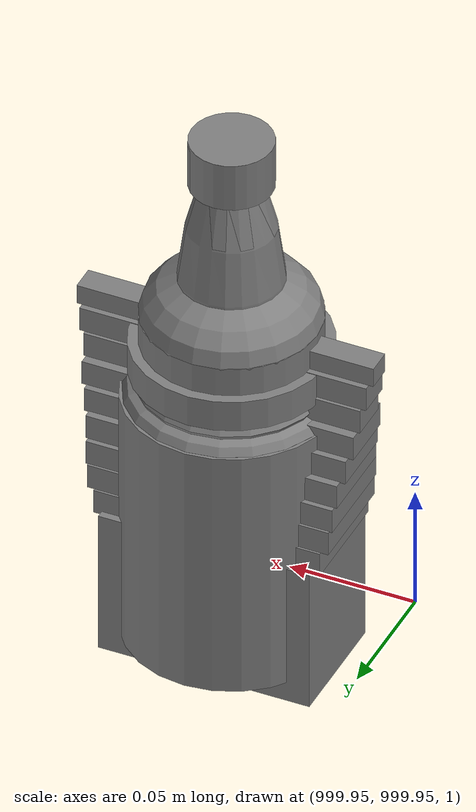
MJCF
<mujoco>
    <option gravity="0.000000000 0.000000000 -9.810000420" timestep="0.0166666" integrator="implicitfast" density="1.225" viscosity="1.8000001e-05" noslip_iterations="10" iterations="100" sdf_iterations="50">
        <flag multiccd="disable"/>
    </option>
    <size memory="1000M"/>
    <compiler coordinate="local"/>
    <worldbody>
        <light cutoff="30" pos="0 1 1" dir="0 -1 -2"/>
        <light cutoff="30" pos="0 -1 1" dir="0 1 -2"/>
        <body pos="0.000000000 0.000000000 0.000000000" euler="0.000000000 0.000000000 0.000000000" name="Interactive Objects_Interactive Objects"/>
        <body pos="1000.000000000 1000.000000000 1.000000000" euler="0.000000000 0.000000000 0.000000000" name="openloong_gripper_2f85_fix_base_usda_salt">
            <geom contype="1" conaffinity="1" density="1000" type="box" material="" rgba="0.500000000 0.500000000 0.500000000 1.000000000" solimp="0.899999976 0.949999988 0.001000000" friction="1.000000000 0.005000000 0.000100000" solref="0.020000000 1.000000000" margin="0" condim="3" group="0" pos="0.000305176 0.000000000 0.084862232" quat="1.000000000 0.000000000 0.000000000 0.000000000" size="0.048999999 0.018999999 0.005000000" name="openloong_gripper_2f85_fix_base_usda_geom_01E093C6_E9CD_458C_BCAF_CC7D1355B90E"/>
            <geom contype="1" conaffinity="1" density="1000" type="box" material="" rgba="0.500000000 0.500000000 0.500000000 1.000000000" solimp="0.899999976 0.949999988 0.001000000" friction="1.000000000 0.005000000 0.000100000" solref="0.020000000 1.000000000" margin="0" condim="3" group="0" pos="0.000305176 0.000000000 0.104564309" quat="1.000000000 0.000000000 0.000000000 0.000000000" size="0.052000001 0.014000000 0.005000000" name="openloong_gripper_2f85_fix_base_usda_geom_8B2B855B_9139_49F9_A89B_7B77FB29281E"/>
            <geom contype="1" conaffinity="1" density="1000" type="box" material="" rgba="0.500000000 0.500000000 0.500000000 1.000000000" solimp="0.899999976 0.949999988 0.001000000" friction="1.000000000 0.005000000 0.000100000" solref="0.020000000 1.000000000" margin="0" condim="3" group="0" pos="0.000305176 0.000000000 0.114487171" quat="1.000000000 0.000000000 0.000000000 0.000000000" size="0.054000001 0.011500000 0.005000000" name="openloong_gripper_2f85_fix_base_usda_geom_32007CCE_EA92_4DB8_892A_784491C6059D"/>
            <geom contype="1" conaffinity="1" density="1000" type="box" material="" rgba="0.500000000 0.500000000 0.500000000 1.000000000" solimp="0.899999976 0.949999988 0.001000000" friction="1.000000000 0.005000000 0.000100000" solref="0.020000000 1.000000000" margin="0" condim="3" group="0" pos="0.000305176 0.000000000 0.075103164" quat="1.000000000 0.000000000 0.000000000 0.000000000" size="0.048000000 0.020000000 0.005000000" name="openloong_gripper_2f85_fix_base_usda_geom_177818CD_452D_4C4D_8770_B7EE9C6D0657"/>
            <geom contype="1" conaffinity="1" density="1000" type="box" material="" rgba="0.500000000 0.500000000 0.500000000 1.000000000" solimp="0.899999976 0.949999988 0.001000000" friction="1.000000000 0.005000000 0.000100000" solref="0.020000000 1.000000000" margin="0" condim="3" group="0" pos="0.000305176 0.000000000 0.134892464" quat="1.000000000 0.000000000 0.000000000 0.000000000" size="0.057000000 0.007000000 0.005000000" name="openloong_gripper_2f85_fix_base_usda_geom_5392557E_FD65_4F31_B24C_0A5EDBCD53DB"/>
            <geom contype="1" conaffinity="1" density="1000" type="box" material="" rgba="0.500000000 0.500000000 0.500000000 1.000000000" solimp="0.899999976 0.949999988 0.001000000" friction="1.000000000 0.005000000 0.000100000" solref="0.020000000 1.000000000" margin="0" condim="3" group="0" pos="0.000305176 0.000000000 0.094920278" quat="1.000000000 0.000000000 0.000000000 0.000000000" size="0.050000001 0.017000001 0.005000000" name="openloong_gripper_2f85_fix_base_usda_geom_8BE90638_D61F_42B8_9724_2245273BF4B5"/>
            <geom contype="1" conaffinity="1" density="1000" type="box" material="" rgba="0.500000000 0.500000000 0.500000000 1.000000000" solimp="0.899999976 0.949999988 0.001000000" friction="1.000000000 0.005000000 0.000100000" solref="0.020000000 1.000000000" margin="0" condim="3" group="0" pos="0.000305176 0.000000000 0.065204859" quat="1.000000000 0.000000000 0.000000000 0.000000000" size="0.045000002 0.021000000 0.005000000" name="openloong_gripper_2f85_fix_base_usda_geom_51023BBA_236A_4D37_885B_694F0D0FCFDD"/>
            <geom contype="1" conaffinity="1" density="1000" type="box" material="" rgba="0.500000000 0.500000000 0.500000000 1.000000000" solimp="0.899999976 0.949999988 0.001000000" friction="1.000000000 0.005000000 0.000100000" solref="0.020000000 1.000000000" margin="0" condim="3" group="0" pos="0.000305176 0.000000000 0.144135714" quat="1.000000000 0.000000000 0.000000000 0.000000000" size="0.059000000 0.005000000 0.004000000" name="openloong_gripper_2f85_fix_base_usda_geom_8016AE2B_5091_4F00_9B67_20EE6EF9C2DD"/>
            <geom contype="1" conaffinity="1" density="1000" type="box" material="" rgba="0.500000000 0.500000000 0.500000000 1.000000000" solimp="0.899999976 0.949999988 0.001000000" friction="1.000000000 0.005000000 0.000100000" solref="0.020000000 1.000000000" margin="0" condim="3" group="0" pos="0.000000000 0.000000000 0.031593561" quat="1.000000000 0.000000000 0.000000000 0.000000000" size="0.041999999 0.024000000 0.029999999" name="openloong_gripper_2f85_fix_base_usda_geom_E758CE07_590B_4C0C_9FB4_3732737CFA49"/>
            <geom contype="1" conaffinity="1" density="1000" type="box" material="" rgba="0.500000000 0.500000000 0.500000000 1.000000000" solimp="0.899999976 0.949999988 0.001000000" friction="1.000000000 0.005000000 0.000100000" solref="0.020000000 1.000000000" margin="0" condim="3" group="0" pos="0.000305176 0.000000000 0.124608755" quat="1.000000000 0.000000000 0.000000000 0.000000000" size="0.055000000 0.008000000 0.005000000" name="openloong_gripper_2f85_fix_base_usda_geom_73AC2770_3C97_41DB_91C0_3828C8C0B0E8"/>
            <freejoint name="openloong_gripper_2f85_fix_base_usda_salt_joint"/>
            <site size="0.005000000 0.005000000 0.005000000" rgba="0.500000000 0.500000000 0.500000000 1.000000000" pos="0.000000000 0.000000000 0.000000000" quat="1.000000000 0.000000000 0.000000000 0.000000000" group="0" type="sphere" name="openloong_gripper_2f85_fix_base_usda_saltsite"/>
        </body>
        <body pos="-2.173039198 6.133007050 1.836238384" euler="70.830276489 -39.594608307 -65.161285400" mocap="true" name="spotlight6_SpotLight"/>
        <body pos="-1.794053435 6.277180195 1.807393789" euler="83.638626099 63.422946930 -107.577133179" mocap="true" name="spotlight5_SpotLight"/>
        <body pos="1000.000000000 1000.000000000 1.000000000" euler="0.000000000 0.000000000 0.000000000" name="openloong_gripper_2f85_fix_base_usda_bottle_red">
            <geom contype="1" conaffinity="1" density="1000" type="ellipsoid" material="" rgba="0.500000000 0.500000000 0.500000000 1.000000000" solimp="0.899999976 0.949999988 0.001000000" friction="1.000000000 0.005000000 0.000100000" solref="0.020000000 1.000000000" margin="0" condim="3" group="0" pos="0.000000000 0.000000000 0.144284487" quat="1.000000000 0.000000000 0.000000000 0.000000000" size="0.021000000 0.021000000 0.079999998" name="openloong_gripper_2f85_fix_base_usda_geom_FFBC17DA_3B75_42C3_B30B_2A9A192C04E7"/>
            <geom contype="1" conaffinity="1" density="1000" type="cylinder" material="" rgba="0.500000000 0.500000000 0.500000000 1.000000000" solimp="0.899999976 0.949999988 0.001000000" friction="1.000000000 0.005000000 0.000100000" solref="0.020000000 1.000000000" margin="0" condim="3" group="0" pos="0.000000000 0.000000000 0.220618963" quat="1.000000000 0.000000000 0.000000000 0.000000000" size="0.016000001 0.010000000 1.000000000" name="openloong_gripper_2f85_fix_base_usda_geom_F73E21C8_6833_4991_9053_CD8C4607FDB8"/>
            <geom contype="1" conaffinity="1" density="1000" type="ellipsoid" material="" rgba="0.500000000 0.500000000 0.500000000 1.000000000" solimp="0.899999976 0.949999988 0.001000000" friction="1.000000000 0.005000000 0.000100000" solref="0.020000000 1.000000000" margin="0" condim="3" group="0" pos="0.000000000 0.000000000 0.118945479" quat="1.000000000 0.000000000 0.000000000 0.000000000" size="0.030999999 0.030999999 0.029999999" name="openloong_gripper_2f85_fix_base_usda_geom_7F6629FE_5BF1_4DB9_8462_A2329B4527A0"/>
            <geom contype="1" conaffinity="1" density="1000" type="box" material="" rgba="0.500000000 0.500000000 0.500000000 1.000000000" solimp="0.899999976 0.949999988 0.001000000" friction="1.000000000 0.005000000 0.000100000" solref="0.020000000 1.000000000" margin="0" condim="3" group="0" pos="0.000000000 0.000000000 0.002189159" quat="1.000000000 0.000000000 0.000000000 0.000000000" size="0.020000000 0.020000000 0.003000000" name="openloong_gripper_2f85_fix_base_usda_geom_EEF1A5AC_B4CD_42B9_9440_5179155E57D1"/>
            <geom contype="1" conaffinity="1" density="1000" type="cylinder" material="" rgba="0.500000000 0.500000000 0.500000000 1.000000000" solimp="0.899999976 0.949999988 0.001000000" friction="1.000000000 0.005000000 0.000100000" solref="0.020000000 1.000000000" margin="0" condim="3" group="0" pos="0.000000000 -0.000366211 0.060884237" quat="1.000000000 0.000000000 0.000000000 0.000000000" size="0.030999999 0.057999998 1.000000000" name="openloong_gripper_2f85_fix_base_usda_geom_3FC4A00D_21B3_4CC3_BBD1_D9FB20DBC0F7"/>
            <freejoint name="openloong_gripper_2f85_fix_base_usda_bottle_red_joint"/>
            <site size="0.005000000 0.005000000 0.005000000" rgba="0.500000000 0.500000000 0.500000000 1.000000000" pos="0.000000000 0.000000000 0.000000000" quat="0.999961913 0.008726535 0.000000000 0.000000000" group="0" type="sphere" name="openloong_gripper_2f85_fix_base_usda_bottle_redsite"/>
        </body>
        <body pos="1000.000000000 1000.000000000 1.000000000" euler="0.000000000 0.000000000 0.000000000" name="openloong_gripper_2f85_fix_base_usda_can">
            <geom contype="1" conaffinity="1" density="1000" type="cylinder" material="" rgba="0.500000000 0.500000000 0.500000000 1.000000000" solimp="0.899999976 0.949999988 0.001000000" friction="1.000000000 0.005000000 0.000100000" solref="0.020000000 1.000000000" margin="0" condim="3" group="0" pos="0.000000000 0.000000000 0.079676986" quat="1.000000000 0.000000000 0.000000000 0.000000000" size="0.034000002 0.071999997 1.000000000" name="openloong_gripper_2f85_fix_base_usda_geom_AFA416C5_4253_419A_8C11_118C5DC5915B"/>
            <geom contype="1" conaffinity="1" density="1000" type="ellipsoid" material="" rgba="0.500000000 0.500000000 0.500000000 1.000000000" solimp="0.899999976 0.949999988 0.001000000" friction="1.000000000 0.005000000 0.000100000" solref="0.020000000 1.000000000" margin="0" condim="3" group="0" pos="0.000000000 0.000000000 0.151854277" quat="1.000000000 0.000000000 0.000000000 0.000000000" size="0.034000002 0.034000002 0.020000000" name="openloong_gripper_2f85_fix_base_usda_geom_B76C1179_C3E7_47AE_955B_CD6A538048FE"/>
            <geom contype="1" conaffinity="1" density="1000" type="box" material="" rgba="0.500000000 0.500000000 0.500000000 1.000000000" solimp="0.899999976 0.949999988 0.001000000" friction="1.000000000 0.005000000 0.000100000" solref="0.020000000 1.000000000" margin="0" condim="3" group="0" pos="0.000000000 0.000000000 0.004777670" quat="1.000000000 0.000000000 0.000000000 0.000000000" size="0.020000000 0.020000000 0.005000000" name="openloong_gripper_2f85_fix_base_usda_geom_003545F4_F644_425F_9C9B_AF36F8C4123F"/>
            <freejoint name="openloong_gripper_2f85_fix_base_usda_can_joint"/>
            <site size="0.005000000 0.005000000 0.005000000" rgba="0.500000000 0.500000000 0.500000000 1.000000000" pos="0.000000000 0.000000000 0.000000000" quat="1.000000000 0.000000000 0.000000000 0.000000000" group="0" type="sphere" name="openloong_gripper_2f85_fix_base_usda_cansite"/>
        </body>
        <body pos="-1.957292080 6.454831123 1.755322576" euler="80.185615540 -49.173221588 -73.927726746" mocap="true" name="spotlight4_SpotLight"/>
        <body pos="1000.000000000 1000.000000000 1.000000000" euler="0.000000000 0.000000000 0.000000000" name="openloong_gripper_2f85_fix_base_usda_jar_01">
            <geom contype="1" conaffinity="1" density="1000" type="box" material="" rgba="0.500000000 0.500000000 0.500000000 1.000000000" solimp="0.899999976 0.949999988 0.001000000" friction="1.000000000 0.005000000 0.000100000" solref="0.020000000 1.000000000" margin="0" condim="3" group="0" pos="0.000000000 0.000000000 0.006158113" quat="1.000000000 0.000000000 0.000000000 0.000000000" size="0.020000000 0.020000000 0.005000000" name="openloong_gripper_2f85_fix_base_usda_geom_4BE56FEB_8CA4_4AC1_BD15_9D405F771620"/>
            <geom contype="1" conaffinity="1" density="1000" type="cylinder" material="" rgba="0.500000000 0.500000000 0.500000000 1.000000000" solimp="0.899999976 0.949999988 0.001000000" friction="1.000000000 0.005000000 0.000100000" solref="0.020000000 1.000000000" margin="0" condim="3" group="0" pos="0.000000000 0.000000000 0.062744498" quat="1.000000000 0.000000000 0.000000000 0.000000000" size="0.041000001 0.052999999 1.000000000" name="openloong_gripper_2f85_fix_base_usda_geom_B48C451E_60AD_4390_8054_DADCFC280F78"/>
            <geom contype="1" conaffinity="1" density="1000" type="ellipsoid" material="" rgba="0.500000000 0.500000000 0.500000000 1.000000000" solimp="0.899999976 0.949999988 0.001000000" friction="1.000000000 0.005000000 0.000100000" solref="0.020000000 1.000000000" margin="0" condim="3" group="0" pos="0.000000000 0.000000000 0.122252703" quat="1.000000000 0.000000000 0.000000000 0.000000000" size="0.035999998 0.035999998 0.010000000" name="openloong_gripper_2f85_fix_base_usda_geom_74ED4F22_CDE7_4991_8637_E4D4BB4AC018"/>
            <geom contype="1" conaffinity="1" density="1000" type="cylinder" material="" rgba="0.500000000 0.500000000 0.500000000 1.000000000" solimp="0.899999976 0.949999988 0.001000000" friction="1.000000000 0.005000000 0.000100000" solref="0.020000000 1.000000000" margin="0" condim="3" group="0" pos="0.000000000 0.000000000 0.015747190" quat="1.000000000 0.000000000 0.000000000 0.000000000" size="0.035000000 0.010000000 1.000000000" name="openloong_gripper_2f85_fix_base_usda_geom_832BD9BE_0FE1_4036_A177_020853701B3A"/>
            <geom contype="1" conaffinity="1" density="1000" type="ellipsoid" material="" rgba="0.500000000 0.500000000 0.500000000 1.000000000" solimp="0.899999976 0.949999988 0.001000000" friction="1.000000000 0.005000000 0.000100000" solref="0.020000000 1.000000000" margin="0" condim="3" group="0" pos="0.000000000 0.000000000 0.115815401" quat="1.000000000 0.000000000 0.000000000 0.000000000" size="0.039999999 0.039999999 0.010000000" name="openloong_gripper_2f85_fix_base_usda_geom_B285B4F0_E975_4014_AFF4_7CB0B9C58771"/>
            <geom contype="1" conaffinity="1" density="1000" type="cylinder" material="" rgba="0.500000000 0.500000000 0.500000000 1.000000000" solimp="0.899999976 0.949999988 0.001000000" friction="1.000000000 0.005000000 0.000100000" solref="0.020000000 1.000000000" margin="0" condim="3" group="0" pos="0.000000000 0.000000000 0.133183479" quat="1.000000000 0.000000000 0.000000000 0.000000000" size="0.037999999 0.006500000 1.000000000" name="openloong_gripper_2f85_fix_base_usda_geom_898EFB94_11BE_49E8_9949_557C4BD18B4C"/>
            <freejoint name="openloong_gripper_2f85_fix_base_usda_jar_01_joint"/>
            <site size="0.005000000 0.005000000 0.005000000" rgba="0.500000000 0.500000000 0.500000000 1.000000000" pos="0.000000000 0.000000000 0.000000000" quat="1.000000000 0.000000000 0.000000000 0.000000000" group="0" type="sphere" name="openloong_gripper_2f85_fix_base_usda_jar_01site"/>
        </body>
        <body pos="1000.000000000 1000.000000000 1.000000000" euler="0.000000000 0.000000000 0.000000000" name="openloong_gripper_2f85_fix_base_usda_bottle_blue">
            <geom contype="1" conaffinity="1" density="1000" type="ellipsoid" material="" rgba="0.500000000 0.500000000 0.500000000 1.000000000" solimp="0.899999976 0.949999988 0.001000000" friction="1.000000000 0.005000000 0.000100000" solref="0.020000000 1.000000000" margin="0" condim="3" group="0" pos="0.000000000 0.000000000 0.118920922" quat="1.000000000 0.000000000 0.000000000 0.000000000" size="0.030999999 0.030999999 0.029999999" name="openloong_gripper_2f85_fix_base_usda_geom_8AB75E76_60D7_452C_B962_27632D0DBE7D"/>
            <geom contype="1" conaffinity="1" density="1000" type="box" material="" rgba="0.500000000 0.500000000 0.500000000 1.000000000" solimp="0.899999976 0.949999988 0.001000000" friction="1.000000000 0.005000000 0.000100000" solref="0.020000000 1.000000000" margin="0" condim="3" group="0" pos="0.000000000 0.000000000 0.002164602" quat="1.000000000 0.000000000 0.000000000 0.000000000" size="0.020000000 0.020000000 0.003000000" name="openloong_gripper_2f85_fix_base_usda_geom_CEA01CBA_18E1_47F7_B123_8FAF5C2353A9"/>
            <geom contype="1" conaffinity="1" density="1000" type="cylinder" material="" rgba="0.500000000 0.500000000 0.500000000 1.000000000" solimp="0.899999976 0.949999988 0.001000000" friction="1.000000000 0.005000000 0.000100000" solref="0.020000000 1.000000000" margin="0" condim="3" group="0" pos="0.000000000 -0.000366211 0.060859680" quat="1.000000000 0.000000000 0.000000000 0.000000000" size="0.030999999 0.057999998 1.000000000" name="openloong_gripper_2f85_fix_base_usda_geom_162D7299_AFCE_4B02_9B8D_EC5F9A3DD0D7"/>
            <geom contype="1" conaffinity="1" density="1000" type="cylinder" material="" rgba="0.500000000 0.500000000 0.500000000 1.000000000" solimp="0.899999976 0.949999988 0.001000000" friction="1.000000000 0.005000000 0.000100000" solref="0.020000000 1.000000000" margin="0" condim="3" group="0" pos="0.000000000 0.000000000 0.220594406" quat="1.000000000 0.000000000 0.000000000 0.000000000" size="0.016000001 0.010000000 1.000000000" name="openloong_gripper_2f85_fix_base_usda_geom_EDB999BD_773B_4FE2_AEA2_618EC527BA13"/>
            <geom contype="1" conaffinity="1" density="1000" type="ellipsoid" material="" rgba="0.500000000 0.500000000 0.500000000 1.000000000" solimp="0.899999976 0.949999988 0.001000000" friction="1.000000000 0.005000000 0.000100000" solref="0.020000000 1.000000000" margin="0" condim="3" group="0" pos="0.000000000 0.000000000 0.144259930" quat="1.000000000 0.000000000 0.000000000 0.000000000" size="0.021000000 0.021000000 0.079999998" name="openloong_gripper_2f85_fix_base_usda_geom_DAF8788A_4073_40C4_9C8C_E6F619E93911"/>
            <freejoint name="openloong_gripper_2f85_fix_base_usda_bottle_blue_joint"/>
            <site size="0.005000000 0.005000000 0.005000000" rgba="0.500000000 0.500000000 0.500000000 1.000000000" pos="0.000000000 0.000000000 0.000000000" quat="0.999961913 0.008726535 0.000000000 0.000000000" group="0" type="sphere" name="openloong_gripper_2f85_fix_base_usda_bottle_bluesite"/>
        </body>
        <body pos="0.000000000 0.000000000 0.000000000" euler="0.000000000 0.000000000 0.000000000" name=" Static Objects_ Static Objects">
            <geom contype="1" conaffinity="1" density="1000" type="box" material="" rgba="0.500000000 0.500000000 0.500000000 1.000000000" solimp="0.899999976 0.949999988 0.001000000" friction="1.000000000 0.005000000 0.000100000" solref="0.020000000 1.000000000" margin="0" condim="3" group="0" pos="-6.286010742 6.153595448 1.563861728" quat="0.707107067 0.000000000 0.000000000 0.707106471" size="0.529999971 3.134999990 0.025000000" name=" Static Objects_geom_C530417E_62B6_4BCC_B4A1_7BD4D3571659"/>
            <geom contype="1" conaffinity="1" density="1000" type="box" material="" rgba="0.500000000 0.500000000 0.500000000 1.000000000" solimp="0.899999976 0.949999988 0.001000000" friction="1.000000000 0.005000000 0.000100000" solref="0.020000000 1.000000000" margin="0" condim="3" group="0" pos="-3.101639986 6.150595188 1.018643856" quat="1.000000000 0.000000000 0.000000000 0.000000000" size="0.050000001 0.579999983 1.019999981" name=" Static Objects_geom_6A4E8E3C_1515_4B34_ACA5_D4908E60E5F8"/>
            <geom contype="1" conaffinity="1" density="1000" type="box" material="" rgba="0.500000000 0.500000000 0.500000000 1.000000000" solimp="0.899999976 0.949999988 0.001000000" friction="1.000000000 0.005000000 0.000100000" solref="0.020000000 1.000000000" margin="0" condim="3" group="0" pos="-2.825197220 6.153595448 1.563861728" quat="0.707107067 0.000000000 0.000000000 0.707106471" size="0.550000012 0.239999995 0.025000000" name=" Static Objects_geom_E0CD998A_003D_430D_9E75_CB8AEDFCF9E0"/>
            <geom contype="1" conaffinity="1" density="1000" type="box" material="" rgba="0.500000000 0.500000000 0.500000000 1.000000000" solimp="0.899999976 0.949999988 0.001000000" friction="1.000000000 0.005000000 0.000100000" solref="0.020000000 1.000000000" margin="0" condim="3" group="0" pos="-6.311686516 6.153595448 1.018643856" quat="0.707107067 0.000000000 0.000000000 0.707106471" size="0.050000001 3.150000095 1.019999981" name=" Static Objects_geom_AE0FED49_4FF2_4B53_9F6B_4362A82CF426"/>
            <geom contype="1" conaffinity="1" density="1000" type="box" material="" rgba="0.500000000 0.500000000 0.500000000 1.000000000" solimp="0.899999976 0.949999988 0.001000000" friction="1.000000000 0.005000000 0.000100000" solref="0.020000000 1.000000000" margin="0" condim="3" group="0" pos="-2.825197220 6.153595448 1.115278244" quat="0.707107067 0.000000000 0.000000000 0.707106471" size="0.550000012 0.239999995 0.025000000" name=" Static Objects_geom_5F2EBB10_799F_4927_A133_7D74ECD6A3B7"/>
            <geom contype="1" conaffinity="1" density="1000" type="box" material="" rgba="0.500000000 0.500000000 0.500000000 1.000000000" solimp="0.899999976 0.949999988 0.001000000" friction="1.000000000 0.005000000 0.000100000" solref="0.020000000 1.000000000" margin="0" condim="3" group="0" pos="-6.293097973 6.153595448 1.114443064" quat="0.707107067 0.000000000 0.000000000 0.707106471" size="0.529999971 3.134999990 0.025000000" name=" Static Objects_geom_89E87253_3F12_48C8_B28A_CCC8DED0C527"/>
            <geom contype="1" conaffinity="1" density="1000" type="box" material="" rgba="0.500000000 0.500000000 0.500000000 1.000000000" solimp="0.899999976 0.949999988 0.001000000" friction="1.000000000 0.005000000 0.000100000" solref="0.020000000 1.000000000" margin="0" condim="3" group="0" pos="-2.825197220 6.153595448 0.629031777" quat="0.707107067 0.000000000 0.000000000 0.707106471" size="0.550000012 0.239999995 0.025000000" name=" Static Objects_geom_0F9CBE30_4E8F_4BE8_8AC8_9AB5BD018F48"/>
            <geom contype="1" conaffinity="1" density="1000" type="box" material="" rgba="0.500000000 0.500000000 0.500000000 1.000000000" solimp="0.899999976 0.949999988 0.001000000" friction="1.000000000 0.005000000 0.000100000" solref="0.020000000 1.000000000" margin="0" condim="3" group="0" pos="-6.286010742 6.153595448 0.096129179" quat="0.707107067 0.000000000 0.000000000 0.707106471" size="0.529999971 3.134999990 0.098999999" name=" Static Objects_geom_D5B503AD_49FA_447D_B829_B08EC224E410"/>
            <geom contype="1" conaffinity="1" density="1000" type="box" material="" rgba="0.500000000 0.500000000 0.500000000 1.000000000" solimp="0.899999976 0.949999988 0.001000000" friction="1.000000000 0.005000000 0.000100000" solref="0.020000000 1.000000000" margin="0" condim="3" group="0" pos="-2.825197220 6.153595448 0.097434282" quat="0.707107067 0.000000000 0.000000000 0.707106471" size="0.550000012 0.239999995 0.098999999" name=" Static Objects_geom_5D9C972B_4B93_4BAE_A7EC_3EF90F56FA57"/>
            <geom contype="1" conaffinity="1" density="1000" type="box" material="" rgba="0.500000000 0.500000000 0.500000000 1.000000000" solimp="0.899999976 0.949999988 0.001000000" friction="1.000000000 0.005000000 0.000100000" solref="0.020000000 1.000000000" margin="0" condim="3" group="0" pos="-6.286010742 6.153595448 0.629031777" quat="0.707107067 0.000000000 0.000000000 0.707106471" size="0.529999971 3.134999990 0.025000000" name=" Static Objects_geom_308662D7_1298_46FD_84AF_0D3B662FB15C"/>
            <geom contype="1" conaffinity="1" density="1000" type="box" material="" rgba="0.500000000 0.500000000 0.500000000 1.000000000" solimp="0.899999976 0.949999988 0.001000000" friction="1.000000000 0.005000000 0.000100000" solref="0.020000000 1.000000000" margin="0" condim="3" group="0" pos="-6.000000000 20.159999847 2.000000000" quat="1.000000000 0.000000000 0.000000000 0.000000000" size="6.079999924 0.070000000 2.000000000" name=" Static Objects_geom_664198B3_E813_4E6B_B5BD_F60D6C6ECB41"/>
            <geom contype="1" conaffinity="1" density="1000" type="box" material="" rgba="0.500000000 0.500000000 0.500000000 1.000000000" solimp="0.899999976 0.949999988 0.001000000" friction="1.000000000 0.005000000 0.000100000" solref="0.020000000 1.000000000" margin="0" condim="3" group="0" pos="-6.000000000 0.035000000 2.000000000" quat="1.000000000 0.000000000 0.000000000 0.000000000" size="6.079999924 0.070000000 2.000000000" name=" Static Objects_geom_79956171_129D_45FA_80F0_57E47C7CB8ED"/>
            <geom contype="1" conaffinity="1" density="1000" type="box" material="" rgba="0.500000000 0.500000000 0.500000000 1.000000000" solimp="0.899999976 0.949999988 0.001000000" friction="1.000000000 0.005000000 0.000100000" solref="0.020000000 1.000000000" margin="0" condim="3" group="0" pos="0.000000000 10.000000000 2.000000000" quat="1.000000000 0.000000000 0.000000000 0.000000000" size="0.070000000 10.500000000 2.000000000" name=" Static Objects_geom_8D5AF6B7_6CD5_4A28_A8C1_7CA5BCF3D8AD"/>
            <geom contype="1" conaffinity="1" density="1000" type="box" material="" rgba="0.500000000 0.500000000 0.500000000 1.000000000" solimp="0.899999976 0.949999988 0.001000000" friction="1.000000000 0.005000000 0.000100000" solref="0.020000000 1.000000000" margin="0" condim="3" group="0" pos="-12.050000191 10.000000000 2.000000000" quat="1.000000000 0.000000000 0.000000000 0.000000000" size="0.070000000 10.500000000 2.000000000" name=" Static Objects_geom_3FA5D7D6_8268_4B9D_B5D9_A0B28E882CAB"/>
            <geom contype="1" conaffinity="1" density="1000" type="plane" material="" rgba="0.500000000 0.500000000 0.500000000 1.000000000" solimp="0.899999976 0.949999988 0.001000000" friction="1.000000000 0.005000000 0.000100000" solref="0.020000000 1.000000000" margin="0" condim="3" group="0" pos="-6.000000000 10.399999619 0.000000000" quat="1.000000000 0.000000000 0.000000000 0.000000000" size="6.050000191 10.800000191 0.010000000" name=" Static Objects_geom_0C87597F_E5AB_4295_92DA_236FE3721A5D"/>
            <geom contype="1" conaffinity="1" density="1000" type="box" material="" rgba="0.500000000 0.500000000 0.500000000 1.000000000" solimp="0.899999976 0.949999988 0.001000000" friction="1.000000000 0.005000000 0.000100000" solref="0.020000000 1.000000000" margin="0" condim="3" group="0" pos="-8.830721855 2.096410990 0.549305558" quat="1.000000000 0.000000000 0.000000000 0.000000000" size="0.280000001 0.430000007 0.550000012" name=" Static Objects_geom_68430322_D078_467A_8B54_7832B1733EF6"/>
            <geom contype="1" conaffinity="1" density="1000" type="box" material="" rgba="0.500000000 0.500000000 0.500000000 1.000000000" solimp="0.899999976 0.949999988 0.001000000" friction="1.000000000 0.005000000 0.000100000" solref="0.020000000 1.000000000" margin="0" condim="3" group="0" pos="-6.460197449 2.937205315 0.548931718" quat="1.000000000 0.000000000 0.000000000 0.000000000" size="2.650000095 0.430000007 0.550000012" name=" Static Objects_geom_040612EC_C689_46A2_BFD8_F6121901F073"/>
            <geom contype="1" conaffinity="1" density="1000" type="box" material="" rgba="0.500000000 0.500000000 0.500000000 1.000000000" solimp="0.899999976 0.949999988 0.001000000" friction="1.000000000 0.005000000 0.000100000" solref="0.020000000 1.000000000" margin="0" condim="3" group="0" pos="-4.240264893 1.327049494 0.549888909" quat="1.000000000 0.000000000 0.000000000 0.000000000" size="0.430000007 1.200000048 0.550000012" name=" Static Objects_geom_12B8F7EC_91E2_42AF_A25A_D49DFB6AE62C"/>
            <geom contype="1" conaffinity="1" density="1000" type="box" material="" rgba="0.500000000 0.500000000 0.500000000 1.000000000" solimp="0.899999976 0.949999988 0.001000000" friction="1.000000000 0.005000000 0.000100000" solref="0.020000000 1.000000000" margin="0" condim="3" group="0" pos="-7.408766270 3.088089943 1.776644945" quat="0.928051054 0.000000000 0.000000000 0.372453064" size="0.050000001 0.100000001 0.050000001" name=" Static Objects_geom_888EA68F_F2C6_4FDC_8D00_43E6C9365F0C"/>
            <geom contype="1" conaffinity="1" density="1000" type="box" material="" rgba="0.500000000 0.500000000 0.500000000 1.000000000" solimp="0.899999976 0.949999988 0.001000000" friction="1.000000000 0.005000000 0.000100000" solref="0.020000000 1.000000000" margin="0" condim="3" group="0" pos="-7.437745571 3.067511320 1.289965630" quat="1.000000000 0.000000000 0.000000000 0.000000000" size="0.029999999 0.020000000 0.020000000" name=" Static Objects_geom_9C3A148E_BC6F_4610_A335_904D5B2C2635"/>
            <geom contype="1" conaffinity="1" density="1000" type="box" material="" rgba="0.500000000 0.500000000 0.500000000 1.000000000" solimp="0.899999976 0.949999988 0.001000000" friction="1.000000000 0.005000000 0.000100000" solref="0.020000000 1.000000000" margin="0" condim="3" group="0" pos="-7.719123363 2.867671013 1.173410416" quat="1.000000000 0.000000000 0.000000000 0.000000000" size="0.250000000 0.250000000 0.079999998" name=" Static Objects_geom_896F2EE6_E8E9_46ED_9723_7D2E2AF6E611"/>
            <geom contype="1" conaffinity="1" density="1000" type="box" material="" rgba="0.500000000 0.500000000 0.500000000 1.000000000" solimp="0.899999976 0.949999988 0.001000000" friction="1.000000000 0.005000000 0.000100000" solref="0.020000000 1.000000000" margin="0" condim="3" group="0" pos="-7.719123363 2.958004713 1.530241251" quat="1.000000000 0.000000000 0.000000000 0.000000000" size="0.250000000 0.159999996 0.280000001" name=" Static Objects_geom_97B9774A_CCCF_47D1_AD00_2622D1878504"/>
            <geom contype="1" conaffinity="1" density="1000" type="cylinder" material="" rgba="0.500000000 0.500000000 0.500000000 1.000000000" solimp="0.899999976 0.949999988 0.001000000" friction="1.000000000 0.005000000 0.000100000" solref="0.020000000 1.000000000" margin="0" condim="3" group="0" pos="-7.427312374 3.069516420 1.502544641" quat="0.928051054 0.000000000 0.000000000 0.372453064" size="0.015000000 0.230000004 0.100000001" name=" Static Objects_geom_AE43D9A6_97E5_4EAC_946E_6531D1E7E117"/>
            <geom contype="1" conaffinity="1" density="1000" type="box" material="" rgba="0.500000000 0.500000000 0.500000000 1.000000000" solimp="0.899999976 0.949999988 0.001000000" friction="1.000000000 0.005000000 0.000100000" solref="0.020000000 1.000000000" margin="0" condim="3" group="0" pos="-9.058088303 6.434794426 1.209077358" quat="1.000000000 0.000000000 0.000000000 0.000000000" size="0.250000000 0.100000001 0.070000000" name=" Static Objects_geom_AFE8F93C_0994_44BE_B312_E38DDB48EA54"/>
            <geom contype="1" conaffinity="1" density="1000" type="box" material="" rgba="0.500000000 0.500000000 0.500000000 1.000000000" solimp="0.899999976 0.949999988 0.001000000" friction="1.000000000 0.005000000 0.000100000" solref="0.020000000 1.000000000" margin="0" condim="3" group="0" pos="-5.611940861 6.318420410 0.350975692" quat="1.000000000 0.000000000 0.000000000 0.000000000" size="0.699999988 0.100000001 0.150000006" name=" Static Objects_geom_A7A597F1_FDD0_4E24_BC59_830579F3064E"/>
            <geom contype="1" conaffinity="1" density="1000" type="box" material="" rgba="0.500000000 0.500000000 0.500000000 1.000000000" solimp="0.899999976 0.949999988 0.001000000" friction="1.000000000 0.005000000 0.000100000" solref="0.020000000 1.000000000" margin="0" condim="3" group="0" pos="-9.237723351 6.464855671 1.209077358" quat="1.000000000 0.000000000 0.000000000 0.000000000" size="0.100000001 0.100000001 0.070000000" name=" Static Objects_geom_E76308A2_54CA_4E6B_8403_0C691AF34396"/>
            <geom contype="1" conaffinity="1" density="1000" type="box" material="" rgba="0.500000000 0.500000000 0.500000000 1.000000000" solimp="0.899999976 0.949999988 0.001000000" friction="1.000000000 0.005000000 0.000100000" solref="0.020000000 1.000000000" margin="0" condim="3" group="0" pos="-6.300771236 6.459744930 1.744376063" quat="1.000000000 0.000000000 0.000000000 0.000000000" size="3.000000000 0.200000003 0.150000006" name=" Static Objects_geom_8A7EB99D_0A20_49E3_952C_F53C0F6FA8E8"/>
            <geom contype="1" conaffinity="1" density="1000" type="box" material="" rgba="0.500000000 0.500000000 0.500000000 1.000000000" solimp="0.899999976 0.949999988 0.001000000" friction="1.000000000 0.005000000 0.000100000" solref="0.020000000 1.000000000" margin="0" condim="3" group="0" pos="-7.373087406 6.458900928 1.214329123" quat="1.000000000 0.000000000 0.000000000 0.000000000" size="0.250000000 0.200000003 0.075000003" name=" Static Objects_geom_9CF45BF4_0ED3_4AA5_B079_3B5E799D8A63"/>
            <geom contype="1" conaffinity="1" density="1000" type="box" material="" rgba="0.500000000 0.500000000 0.500000000 1.000000000" solimp="0.899999976 0.949999988 0.001000000" friction="1.000000000 0.005000000 0.000100000" solref="0.020000000 1.000000000" margin="0" condim="3" group="0" pos="-4.035642624 6.459744930 0.352518857" quat="1.000000000 0.000000000 0.000000000 0.000000000" size="0.800000012 0.200000003 0.150000006" name=" Static Objects_geom_028BC5A1_B919_43C8_B6A5_FC2B89C6056E"/>
            <geom contype="1" conaffinity="1" density="1000" type="box" material="" rgba="0.500000000 0.500000000 0.500000000 1.000000000" solimp="0.899999976 0.949999988 0.001000000" friction="1.000000000 0.005000000 0.000100000" solref="0.020000000 1.000000000" margin="0" condim="3" group="0" pos="-3.907610416 6.318625927 0.800981164" quat="1.000000000 0.000000000 0.000000000 0.000000000" size="0.500000000 0.100000001 0.150000006" name=" Static Objects_geom_ACB3CE7F_BE21_4434_BE85_423D7E19A533"/>
            <geom contype="1" conaffinity="1" density="1000" type="box" material="" rgba="0.500000000 0.500000000 0.500000000 1.000000000" solimp="0.899999976 0.949999988 0.001000000" friction="1.000000000 0.005000000 0.000100000" solref="0.020000000 1.000000000" margin="0" condim="3" group="0" pos="-6.098561764 6.327973843 1.292199373" quat="1.000000000 0.000000000 0.000000000 0.000000000" size="0.500000000 0.100000001 0.150000006" name=" Static Objects_geom_7B051375_EB44_43AC_88D1_FD019E535C40"/>
            <geom contype="1" conaffinity="1" density="1000" type="box" material="" rgba="0.500000000 0.500000000 0.500000000 1.000000000" solimp="0.899999976 0.949999988 0.001000000" friction="1.000000000 0.005000000 0.000100000" solref="0.020000000 1.000000000" margin="0" condim="3" group="0" pos="-7.886891365 6.459744930 0.352518857" quat="1.000000000 0.000000000 0.000000000 0.000000000" size="1.500000000 0.200000003 0.150000006" name=" Static Objects_geom_AB5F5505_87C0_48A7_87AF_B00026BDD9D5"/>
            <geom contype="1" conaffinity="1" density="1000" type="box" material="" rgba="0.500000000 0.500000000 0.500000000 1.000000000" solimp="0.899999976 0.949999988 0.001000000" friction="1.000000000 0.005000000 0.000100000" solref="0.020000000 1.000000000" margin="0" condim="3" group="0" pos="-6.824534416 6.447464466 1.212718010" quat="1.000000000 0.000000000 0.000000000 0.000000000" size="0.100000001 0.100000001 0.075000003" name=" Static Objects_geom_23DCC827_3D6A_4E20_8B4A_21D7DB83CCDD"/>
            <geom contype="1" conaffinity="1" density="1000" type="box" material="" rgba="0.500000000 0.500000000 0.500000000 1.000000000" solimp="0.899999976 0.949999988 0.001000000" friction="1.000000000 0.005000000 0.000100000" solref="0.020000000 1.000000000" margin="0" condim="3" group="0" pos="-4.407354832 6.459744930 1.292199373" quat="1.000000000 0.000000000 0.000000000 0.000000000" size="1.240000010 0.200000003 0.150000006" name=" Static Objects_geom_D03D97B3_E5DF_4F29_8A38_5E928D7290F4"/>
            <geom contype="1" conaffinity="1" density="1000" type="box" material="" rgba="0.500000000 0.500000000 0.500000000 1.000000000" solimp="0.899999976 0.949999988 0.001000000" friction="1.000000000 0.005000000 0.000100000" solref="0.020000000 1.000000000" margin="0" condim="3" group="0" pos="-6.751636982 6.459744930 0.800981164" quat="1.000000000 0.000000000 0.000000000 0.000000000" size="2.200000048 0.200000003 0.150000006" name=" Static Objects_geom_490C8E5E_938C_42BE_BF1E_6BDA18FE4CF4"/>
            <geom contype="1" conaffinity="1" density="1000" type="box" material="" rgba="0.500000000 0.500000000 0.500000000 1.000000000" solimp="0.899999976 0.949999988 0.001000000" friction="1.000000000 0.005000000 0.000100000" solref="0.020000000 1.000000000" margin="0" condim="3" group="0" pos="-6.924745083 6.362090111 1.214329123" quat="1.000000000 0.000000000 0.000000000 0.000000000" size="0.200000003 0.100000001 0.075000003" name=" Static Objects_geom_560BF6F3_2CD0_454E_94A2_17280B86D481"/>
            <geom contype="1" conaffinity="1" density="1000" type="box" material="" rgba="0.500000000 0.500000000 0.500000000 1.000000000" solimp="0.899999976 0.949999988 0.001000000" friction="1.000000000 0.005000000 0.000100000" solref="0.020000000 1.000000000" margin="0" condim="3" group="0" pos="-8.844120979 6.464855671 1.209077358" quat="1.000000000 0.000000000 0.000000000 0.000000000" size="0.100000001 0.100000001 0.070000000" name=" Static Objects_geom_C9A66419_5C06_4C6D_A6CB_998E7F647F76"/>
            <geom contype="1" conaffinity="1" density="1000" type="box" material="" rgba="0.500000000 0.500000000 0.500000000 1.000000000" solimp="0.899999976 0.949999988 0.001000000" friction="1.000000000 0.005000000 0.000100000" solref="0.020000000 1.000000000" margin="0" condim="3" group="0" pos="-3.157672644 6.136868477 1.348373055" quat="1.000000000 0.000000000 0.000000000 0.000000000" size="0.200000003 0.519999981 0.300000012" name=" Static Objects_geom_EA96C30A_3AEA_412B_A8CD_AB2AC2CA0557"/>
        </body>
        <body pos="-6.332345009 2.779978037 1.034067392" euler="0.000000000 0.000000000 0.000000000" name="openloong_gripper_2f85_fix_base_usda_basket">
            <geom contype="1" conaffinity="1" density="100000" type="box" material="" rgba="0.500000000 0.500000000 0.500000000 1.000000000" solimp="0.899999976 0.949999988 0.001000000" friction="1.000000000 0.899999976 0.000100000" solref="0.020000000 1.000000000" margin="0" condim="3" group="0" pos="-0.039724827 -0.188568115 0.167089701" quat="0.997537494 0.070135131 0.000000000 0.000000000" size="0.150000006 0.006000000 0.108000003" name="openloong_gripper_2f85_fix_base_usda_geom_7B81CEEB_2089_4CBA_ACF9_11981EA4F812"/>
            <geom contype="1" conaffinity="1" density="100000" type="box" material="" rgba="0.500000000 0.500000000 0.500000000 1.000000000" solimp="0.899999976 0.949999988 0.001000000" friction="1.000000000 0.899999976 0.000100000" solref="0.020000000 1.000000000" margin="0" condim="3" group="0" pos="0.094372749 0.000000000 0.168361664" quat="0.706172049 0.036353335 0.036353379 0.706171215" size="0.200000003 0.006000000 0.108000003" name="openloong_gripper_2f85_fix_base_usda_geom_B3ACE474_78AE_4618_B424_6015EE62B060"/>
            <geom contype="1" conaffinity="1" density="100000" type="box" material="" rgba="0.500000000 0.500000000 0.500000000 1.000000000" solimp="0.899999976 0.949999988 0.001000000" friction="1.000000000 0.899999976 0.000100000" solref="0.020000000 1.000000000" margin="0" condim="3" group="0" pos="-0.039724827 0.000000000 0.068126202" quat="1.000000000 0.000000000 0.000000000 0.000000000" size="0.129999995 0.174999997 0.006000000" name="openloong_gripper_2f85_fix_base_usda_geom_1E5AE144_5AE6_4D5C_A1C9_D88FF66C0E2B"/>
            <geom contype="1" conaffinity="1" density="100000" type="box" material="" rgba="0.500000000 0.500000000 0.500000000 1.000000000" solimp="0.899999976 0.949999988 0.001000000" friction="1.000000000 0.899999976 0.000100000" solref="0.020000000 1.000000000" margin="0" condim="3" group="0" pos="-0.039724827 0.188377380 0.167089701" quat="0.997489929 -0.070808925 0.000000000 0.000000000" size="0.150000006 0.006000000 0.108000003" name="openloong_gripper_2f85_fix_base_usda_geom_D49A5FB0_8269_440B_B9A6_1C2005AC65A8"/>
            <geom contype="1" conaffinity="1" density="100000" type="box" material="" rgba="0.500000000 0.500000000 0.500000000 1.000000000" solimp="0.899999976 0.949999988 0.001000000" friction="1.000000000 0.899999976 0.000100000" solref="0.020000000 1.000000000" margin="0" condim="3" group="0" pos="-0.172339439 0.000000000 0.168361664" quat="0.706172407 -0.036353018 -0.036353093 0.706170976" size="0.200000003 0.006000000 0.108000003" name="openloong_gripper_2f85_fix_base_usda_geom_8EE2121D_895B_43C4_8609_57C5B9C3B17A"/>
            <freejoint name="openloong_gripper_2f85_fix_base_usda_basket_joint"/>
            <site size="0.005000000 0.005000000 0.005000000" rgba="0.500000000 0.500000000 0.500000000 1.000000000" pos="0.000000000 0.000000000 0.000000000" quat="1.000000000 0.000000000 0.000000000 0.000000000" group="0" type="sphere" name="openloong_gripper_2f85_fix_base_usda_basketsite"/>
        </body>
        <body pos="-3.510578632 3.403555870 -0.000000100" euler="0.000000000 0.000000000 40.200675964" name="openloong_gripper_2f85_fix_base_usda_PZ">
            <geom contype="1" conaffinity="1" density="1000" type="box" material="" rgba="0.500000000 0.500000000 0.500000000 1.000000000" solimp="0.899999976 0.949999988 0.001000000" friction="1.000000000 0.005000000 0.000100000" solref="0.020000000 1.000000000" margin="0" condim="3" group="0" pos="-0.047453165 0.056484699 0.373715430" quat="0.934750080 0.077914521 0.028795123 0.345459938" size="0.180000007 0.010000000 0.379999995" name="openloong_gripper_2f85_fix_base_usda_geom_994014FA_C43B_4ECE_B08E_D7789B372D85"/>
            <geom contype="1" conaffinity="1" density="1000" type="box" material="" rgba="0.500000000 0.500000000 0.500000000 1.000000000" solimp="0.899999976 0.949999988 0.001000000" friction="1.000000000 0.005000000 0.000100000" solref="0.020000000 1.000000000" margin="0" condim="3" group="0" pos="0.047452450 -0.054376602 0.374072611" quat="0.934387863 -0.082143910 -0.030358355 0.345326364" size="0.180000007 0.010000000 0.379999995" name="openloong_gripper_2f85_fix_base_usda_geom_323C776A_D7F6_4EFD_A42B_598DE550AC5F"/>
            <freejoint name="openloong_gripper_2f85_fix_base_usda_PZ"/>
        </body>
        <body pos="-7.168000221 2.823999882 1.227496982" euler="-0.283413976 0.056829724 -0.133293271" name="openloong_gripper_2f85_fix_base_usda_Pos">
            <geom contype="1" conaffinity="1" density="1000" type="box" material="" rgba="0.500000000 0.500000000 0.500000000 1.000000000" solimp="0.899999976 0.949999988 0.001000000" friction="1.000000000 0.005000000 0.000100000" solref="0.020000000 1.000000000" margin="0" condim="3" group="0" pos="-0.002278805 0.074524641 -0.004134059" quat="0.315989345 0.948763072 -0.000000000 0.000000000" size="0.059999999 0.013000000 0.035000000" name="openloong_gripper_2f85_fix_base_usda_geom_16850C22_CB62_4581_828C_1CCAE2934285"/>
            <geom contype="1" conaffinity="1" density="1000" type="box" material="" rgba="0.500000000 0.500000000 0.500000000 1.000000000" solimp="0.899999976 0.949999988 0.001000000" friction="1.000000000 0.005000000 0.000100000" solref="0.020000000 1.000000000" margin="0" condim="3" group="0" pos="-0.002278805 0.078031301 0.008128285" quat="0.990447521 -0.137893379 -0.000000000 -0.000000000" size="0.059999999 0.010000000 0.035000000" name="openloong_gripper_2f85_fix_base_usda_geom_37FB83CA_2B88_4469_B34A_2591769E226B"/>
            <geom contype="1" conaffinity="1" density="1000" type="box" material="" rgba="0.500000000 0.500000000 0.500000000 1.000000000" solimp="0.899999976 0.949999988 0.001000000" friction="1.000000000 0.005000000 0.000100000" solref="0.020000000 1.000000000" margin="0" condim="3" group="0" pos="-0.002278805 0.080785275 -0.002596974" quat="0.287325472 -0.957833409 0.000000000 -0.000000000" size="0.059999999 0.013000000 0.035000000" name="openloong_gripper_2f85_fix_base_usda_geom_F8B755A5_471E_440E_9545_2D3CBC5A4477"/>
            <geom contype="1" conaffinity="1" density="1000" type="box" material="" rgba="0.500000000 0.500000000 0.500000000 1.000000000" solimp="0.899999976 0.949999988 0.001000000" friction="1.000000000 0.005000000 0.000100000" solref="0.020000000 1.000000000" margin="0" condim="3" group="0" pos="-0.002278805 -0.098804474 -0.020146966" quat="0.988851666 0.148906454 0.000000000 -0.000000000" size="0.059999999 0.022000000 0.020000000" name="openloong_gripper_2f85_fix_base_usda_geom_710DBF2F_1291_471E_A1CC_4C8F233E3800"/>
            <geom contype="1" conaffinity="1" density="1000" type="box" material="" rgba="0.500000000 0.500000000 0.500000000 1.000000000" solimp="0.899999976 0.949999988 0.001000000" friction="1.000000000 0.005000000 0.000100000" solref="0.020000000 1.000000000" margin="0" condim="3" group="0" pos="-0.002279282 0.019920111 0.012102962" quat="0.995421767 0.095583342 -0.000000000 -0.000000000" size="0.059999999 0.025000000 0.026000001" name="openloong_gripper_2f85_fix_base_usda_geom_58B566AC_0A89_4A65_8908_D290D5EA4846"/>
            <geom contype="1" conaffinity="1" density="1000" type="box" material="" rgba="0.500000000 0.500000000 0.500000000 1.000000000" solimp="0.899999976 0.949999988 0.001000000" friction="1.000000000 0.005000000 0.000100000" solref="0.020000000 1.000000000" margin="0" condim="3" group="0" pos="-0.002279282 0.005734444 -0.014276862" quat="0.999571741 -0.029275302 -0.000000000 -0.000000000" size="0.059999999 0.050000001 0.010000000" name="openloong_gripper_2f85_fix_base_usda_geom_D6FA5DA5_5A94_4E15_84D1_74B0B71FF247"/>
            <geom contype="1" conaffinity="1" density="1000" type="box" material="" rgba="0.500000000 0.500000000 0.500000000 1.000000000" solimp="0.899999976 0.949999988 0.001000000" friction="1.000000000 0.005000000 0.000100000" solref="0.020000000 1.000000000" margin="0" condim="3" group="0" pos="-0.002278805 0.079460382 0.007771969" quat="0.922590554 -0.385781586 0.000000000 -0.000000000" size="0.059999999 0.010000000 0.035000000" name="openloong_gripper_2f85_fix_base_usda_geom_7B69AB1F_166B_436E_B943_3D10F520129F"/>
            <geom contype="1" conaffinity="1" density="1000" type="box" material="" rgba="0.500000000 0.500000000 0.500000000 1.000000000" solimp="0.899999976 0.949999988 0.001000000" friction="1.000000000 0.005000000 0.000100000" solref="0.020000000 1.000000000" margin="0" condim="3" group="0" pos="-0.002279282 0.081384182 -0.001320124" quat="0.590483785 -0.807049930 0.000000000 -0.000000000" size="0.059999999 0.013000000 0.035000000" name="openloong_gripper_2f85_fix_base_usda_geom_C9779296_609B_4544_AD2B_3D2C3D1B024E"/>
            <geom contype="1" conaffinity="1" density="1000" type="box" material="" rgba="0.500000000 0.500000000 0.500000000 1.000000000" solimp="0.899999976 0.949999988 0.001000000" friction="1.000000000 0.005000000 0.000100000" solref="0.020000000 1.000000000" margin="0" condim="3" group="0" pos="-0.002278805 -0.059297800 -0.007972836" quat="0.988851666 0.148906454 0.000000000 -0.000000000" size="0.059999999 0.020000000 0.022000000" name="openloong_gripper_2f85_fix_base_usda_geom_C17057C8_ABF5_47E5_BFE5_A2BFF7CFC7F0"/>
            <geom contype="1" conaffinity="1" density="1000" type="box" material="" rgba="0.500000000 0.500000000 0.500000000 1.000000000" solimp="0.899999976 0.949999988 0.001000000" friction="1.000000000 0.005000000 0.000100000" solref="0.020000000 1.000000000" margin="0" condim="3" group="0" pos="-0.002278805 0.076618671 -0.004656792" quat="0.004634961 0.999989629 -0.000000000 0.000000000" size="0.059999999 0.013000000 0.035000000" name="openloong_gripper_2f85_fix_base_usda_geom_745BFC59_0F7D_4C1E_A12D_9578073A681F"/>
            <geom contype="1" conaffinity="1" density="1000" type="box" material="" rgba="0.500000000 0.500000000 0.500000000 1.000000000" solimp="0.899999976 0.949999988 0.001000000" friction="1.000000000 0.005000000 0.000100000" solref="0.020000000 1.000000000" margin="0" condim="3" group="0" pos="-0.002279282 -0.021952629 0.002960086" quat="0.991270423 0.131847665 -0.000000000 0.000000000" size="0.059999999 0.020000000 0.024000000" name="openloong_gripper_2f85_fix_base_usda_geom_C0709195_4992_4906_B8CA_DA408E43FF07"/>
            <geom contype="1" conaffinity="1" density="1000" type="box" material="" rgba="0.500000000 0.500000000 0.500000000 1.000000000" solimp="0.899999976 0.949999988 0.001000000" friction="1.000000000 0.005000000 0.000100000" solref="0.020000000 1.000000000" margin="0" condim="3" group="0" pos="-0.002278805 0.081418991 0.002587914" quat="0.803492308 -0.595315695 0.000000000 -0.000000000" size="0.059999999 0.013000000 0.035000000" name="openloong_gripper_2f85_fix_base_usda_geom_A8CCD5D4_0094_4E54_989E_42B8DFDE8C24"/>
            <geom contype="1" conaffinity="1" density="1000" type="box" material="" rgba="0.500000000 0.500000000 0.500000000 1.000000000" solimp="0.899999976 0.949999988 0.001000000" friction="1.000000000 0.005000000 0.000100000" solref="0.020000000 1.000000000" margin="0" condim="3" group="0" pos="-0.002278805 0.061115503 0.008545756" quat="0.999326169 0.036714450 0.000000000 -0.000000000" size="0.059999999 0.020000000 0.035000000" name="openloong_gripper_2f85_fix_base_usda_geom_B99120A1_59ED_4FDC_A316_37DB45C6F4AD"/>
            <freejoint name="openloong_gripper_2f85_fix_base_usda_pos_scan"/>
        </body>
        <body pos="-2.436573029 6.404376507 0.137849092" euler="0.000000000 0.000000000 0.000000000" name="openloong_gripper_2f85_fix_base_usda_shoppingtrolley_01">
            <geom contype="1" conaffinity="1" density="1000" type="box" material="" rgba="0.500000000 0.500000000 0.500000000 1.000000000" solimp="0.899999976 0.949999988 0.001000000" friction="1.000000000 0.005000000 0.000100000" solref="0.020000000 1.000000000" margin="0" condim="3" group="0" pos="-0.107458733 0.238907143 0.911498845" quat="0.634576976 0.622505128 -0.330067992 -0.317575932" size="0.017999999 0.022499999 0.035999998" name="openloong_gripper_2f85_fix_base_usda_geom_EDD95DA2_9CCE_437D_8ACE_CA1470DB8672"/>
            <geom contype="1" conaffinity="1" density="1000" type="box" material="" rgba="0.500000000 0.500000000 0.500000000 1.000000000" solimp="0.899999976 0.949999988 0.001000000" friction="1.000000000 0.005000000 0.000100000" solref="0.020000000 1.000000000" margin="0" condim="3" group="0" pos="-0.126757339 -0.182533979 0.598989725" quat="0.996607184 0.055331606 -0.059003651 -0.015205891" size="0.013499999 0.287999988 0.053999998" name="openloong_gripper_2f85_fix_base_usda_geom_692BE576_3605_42A2_BE30_22F6C9F2EFCE"/>
            <geom contype="1" conaffinity="1" density="1000" type="box" material="" rgba="0.500000000 0.500000000 0.500000000 1.000000000" solimp="0.899999976 0.949999988 0.001000000" friction="1.000000000 0.005000000 0.000100000" solref="0.020000000 1.000000000" margin="0" condim="3" group="0" pos="-0.005004787 0.248085022 0.912686050" quat="1.000000000 0.000000000 0.000000000 0.000000000" size="0.107999995 0.022499999 0.022499999" name="openloong_gripper_2f85_fix_base_usda_geom_ECEA655C_5FB2_4FAB_A463_BFE9EFC56190"/>
            <geom contype="1" conaffinity="1" density="1000" type="box" material="" rgba="0.500000000 0.500000000 0.500000000 1.000000000" solimp="0.899999976 0.949999988 0.001000000" friction="1.000000000 0.005000000 0.000100000" solref="0.020000000 1.000000000" margin="0" condim="3" group="0" pos="-0.169898406 -0.043119621 0.915120542" quat="0.687021017 0.726584017 -0.005590606 -0.006832919" size="0.017999999 0.022499999 0.089999996" name="openloong_gripper_2f85_fix_base_usda_geom_BD3A4E2C_00FD_4599_A9A9_249AE879D003"/>
            <geom contype="1" conaffinity="1" density="1000" type="box" material="" rgba="0.500000000 0.500000000 0.500000000 1.000000000" solimp="0.899999976 0.949999988 0.001000000" friction="1.000000000 0.005000000 0.000100000" solref="0.020000000 1.000000000" margin="0" condim="3" group="0" pos="0.148195267 -0.199506566 0.782808602" quat="0.998808920 0.017156634 0.026950166 0.036880098" size="0.013499999 0.305999994 0.063000001" name="openloong_gripper_2f85_fix_base_usda_geom_EFA48EBE_DEAE_4E6F_A21C_CAE7945E2E84"/>
            <geom contype="1" conaffinity="1" density="1000" type="box" material="" rgba="0.500000000 0.500000000 0.500000000 1.000000000" solimp="0.899999976 0.949999988 0.001000000" friction="1.000000000 0.005000000 0.000100000" solref="0.020000000 1.000000000" margin="0" condim="3" group="0" pos="-0.142927840 -0.199506134 0.784674108" quat="0.998421252 0.016904408 -0.027109101 -0.046199299" size="0.013499999 0.305999994 0.063000001" name="openloong_gripper_2f85_fix_base_usda_geom_E8811779_B674_4C76_9BD2_BBA8E927556F"/>
            <geom contype="1" conaffinity="1" density="1000" type="box" material="" rgba="0.500000000 0.500000000 0.500000000 1.000000000" solimp="0.899999976 0.949999988 0.001000000" friction="1.000000000 0.005000000 0.000100000" solref="0.020000000 1.000000000" margin="0" condim="3" group="0" pos="-0.000004721 -0.174527690 0.560063601" quat="0.996704638 0.081116498 -0.000000004 0.000000000" size="0.126000002 0.287999988 0.009000000" name="openloong_gripper_2f85_fix_base_usda_geom_810C81D4_7B09_4B19_8E63_F88CF7018DE4"/>
            <geom contype="1" conaffinity="1" density="1000" type="box" material="" rgba="0.500000000 0.500000000 0.500000000 1.000000000" solimp="0.899999976 0.949999988 0.001000000" friction="1.000000000 0.005000000 0.000100000" solref="0.020000000 1.000000000" margin="0" condim="3" group="0" pos="-0.160832763 0.103427693 0.910528183" quat="0.711469591 0.699786782 -0.048386075 -0.042050660" size="0.017999999 0.022499999 0.071999997" name="openloong_gripper_2f85_fix_base_usda_geom_E7220D3F_DAC8_4A4E_815A_8011E653C49E"/>
            <geom contype="1" conaffinity="1" density="1000" type="box" material="" rgba="0.500000000 0.500000000 0.500000000 1.000000000" solimp="0.899999976 0.949999988 0.001000000" friction="1.000000000 0.005000000 0.000100000" solref="0.020000000 1.000000000" margin="0" condim="3" group="0" pos="-0.169898406 -0.178061336 0.864131629" quat="0.916343808 -0.400392294 -0.000000045 0.000000030" size="0.017999999 0.022499999 0.089999996" name="openloong_gripper_2f85_fix_base_usda_geom_B0EC6C7C_0A10_4A10_81F2_D1E48EC72764"/>
            <geom contype="1" conaffinity="1" density="1000" type="box" material="" rgba="0.500000000 0.500000000 0.500000000 1.000000000" solimp="0.899999976 0.949999988 0.001000000" friction="1.000000000 0.005000000 0.000100000" solref="0.020000000 1.000000000" margin="0" condim="3" group="0" pos="-0.000006008 -0.484932661 0.670727849" quat="0.997585475 0.069449045 -0.000000004 -0.000000089" size="0.179999992 0.013499999 0.170999989" name="openloong_gripper_2f85_fix_base_usda_geom_2757222F_A341_4C2B_A747_182E8E5C4C2C"/>
            <geom contype="1" conaffinity="1" density="1000" type="box" material="" rgba="0.500000000 0.500000000 0.500000000 1.000000000" solimp="0.899999976 0.949999988 0.001000000" friction="1.000000000 0.005000000 0.000100000" solref="0.020000000 1.000000000" margin="0" condim="3" group="0" pos="0.134013891 0.200098798 0.912192523" quat="0.692574680 -0.680924535 -0.166899428 0.169783980" size="0.017999999 0.022499999 0.035999998" name="openloong_gripper_2f85_fix_base_usda_geom_811ACA51_99BB_44E1_8C7B_923C0D5F4EE9"/>
            <geom contype="1" conaffinity="1" density="1000" type="box" material="" rgba="0.500000000 0.500000000 0.500000000 1.000000000" solimp="0.899999976 0.949999988 0.001000000" friction="1.000000000 0.005000000 0.000100000" solref="0.020000000 1.000000000" margin="0" condim="3" group="0" pos="0.141839072 -0.191051379 0.702451229" quat="0.997147262 0.056065105 0.045779929 0.021407485" size="0.013499999 0.287999988 0.053999998" name="openloong_gripper_2f85_fix_base_usda_geom_BD8626E6_D932_4323_BCB0_E90D1138B764"/>
            <geom contype="1" conaffinity="1" density="1000" type="box" material="" rgba="0.500000000 0.500000000 0.500000000 1.000000000" solimp="0.899999976 0.949999988 0.001000000" friction="1.000000000 0.005000000 0.000100000" solref="0.020000000 1.000000000" margin="0" condim="3" group="0" pos="0.169898629 -0.178061336 0.864131629" quat="0.916343808 -0.400392294 -0.000000045 0.000000030" size="0.017999999 0.022499999 0.089999996" name="openloong_gripper_2f85_fix_base_usda_geom_E4303458_46BE_4965_AC40_1AD2707F3028"/>
            <geom contype="1" conaffinity="1" density="1000" type="box" material="" rgba="0.500000000 0.500000000 0.500000000 1.000000000" solimp="0.899999976 0.949999988 0.001000000" friction="1.000000000 0.005000000 0.000100000" solref="0.020000000 1.000000000" margin="0" condim="3" group="0" pos="-0.000005364 0.100332208 0.734785020" quat="0.999668717 0.025737956 -0.000000010 0.000000000" size="0.135000005 0.019800000 0.152999997" name="openloong_gripper_2f85_fix_base_usda_geom_8C9746D1_D7F4_43D5_8FE2_C8E19FF6AB58"/>
            <geom contype="1" conaffinity="1" density="1000" type="box" material="" rgba="0.500000000 0.500000000 0.500000000 1.000000000" solimp="0.899999976 0.949999988 0.001000000" friction="1.000000000 0.005000000 0.000100000" solref="0.020000000 1.000000000" margin="0" condim="3" group="0" pos="-0.012634277 -0.174527690 -0.088243507" quat="1.000000000 0.000000000 -0.000000004 0.000000000" size="0.135000005 0.287999988 0.044999998" name="openloong_gripper_2f85_fix_base_usda_geom_2F1D7A19_7B46_4314_9316_CDFBD4554429"/>
            <geom contype="1" conaffinity="1" density="1000" type="box" material="" rgba="0.500000000 0.500000000 0.500000000 1.000000000" solimp="0.899999976 0.949999988 0.001000000" friction="1.000000000 0.005000000 0.000100000" solref="0.020000000 1.000000000" margin="0" condim="3" group="0" pos="0.131482959 -0.182533979 0.598989725" quat="0.996607125 0.055331629 0.059003670 0.015205893" size="0.013499999 0.287999988 0.053999998" name="openloong_gripper_2f85_fix_base_usda_geom_DB4E9422_A67B_4694_9831_1DAF94E9F071"/>
            <geom contype="1" conaffinity="1" density="1000" type="box" material="" rgba="0.500000000 0.500000000 0.500000000 1.000000000" solimp="0.899999976 0.949999988 0.001000000" friction="1.000000000 0.005000000 0.000100000" solref="0.020000000 1.000000000" margin="0" condim="3" group="0" pos="0.103667587 0.233050480 0.912927270" quat="0.634205043 -0.622199059 -0.324503720 0.324576139" size="0.017999999 0.022499999 0.035999998" name="openloong_gripper_2f85_fix_base_usda_geom_979C7144_2BE7_4CA3_828B_90F3D8C84B35"/>
            <geom contype="1" conaffinity="1" density="1000" type="box" material="" rgba="0.500000000 0.500000000 0.500000000 1.000000000" solimp="0.899999976 0.949999988 0.001000000" friction="1.000000000 0.005000000 0.000100000" solref="0.020000000 1.000000000" margin="0" condim="3" group="0" pos="-0.134013891 0.200098798 0.912192523" quat="0.694057047 0.679413557 -0.172947660 -0.163618833" size="0.017999999 0.022499999 0.035999998" name="openloong_gripper_2f85_fix_base_usda_geom_439443E4_B5A8_4A12_A4DF_F223977FC0C5"/>
            <geom contype="1" conaffinity="1" density="1000" type="box" material="" rgba="0.500000000 0.500000000 0.500000000 1.000000000" solimp="0.899999976 0.949999988 0.001000000" friction="1.000000000 0.005000000 0.000100000" solref="0.020000000 1.000000000" margin="0" condim="3" group="0" pos="-0.135714188 -0.191051379 0.694841146" quat="0.997147322 0.056064609 -0.045779683 -0.021407485" size="0.013499999 0.287999988 0.053999998" name="openloong_gripper_2f85_fix_base_usda_geom_24627575_FFEE_4207_8EC3_14954974E2C4"/>
            <geom contype="1" conaffinity="1" density="1000" type="box" material="" rgba="0.500000000 0.500000000 0.500000000 1.000000000" solimp="0.899999976 0.949999988 0.001000000" friction="1.000000000 0.005000000 0.000100000" solref="0.020000000 1.000000000" margin="0" condim="3" group="0" pos="0.169898629 -0.043119621 0.915120542" quat="0.687029123 -0.726576388 -0.006509603 0.005963952" size="0.017999999 0.022499999 0.089999996" name="openloong_gripper_2f85_fix_base_usda_geom_49D2F490_9551_4C3C_95B8_50E23AF6BB67"/>
            <geom contype="1" conaffinity="1" density="1000" type="box" material="" rgba="0.500000000 0.500000000 0.500000000 1.000000000" solimp="0.899999976 0.949999988 0.001000000" friction="1.000000000 0.005000000 0.000100000" solref="0.020000000 1.000000000" margin="0" condim="3" group="0" pos="0.160832971 0.103427693 0.910528183" quat="0.711112797 -0.700149298 -0.042821646 0.047705106" size="0.017999999 0.022499999 0.071999997" name="openloong_gripper_2f85_fix_base_usda_geom_BC2DBC12_64D3_43E7_B59A_77BA3078BAA8"/>
            <freejoint name="openloong_gripper_2f85_fix_base_usda_shoppingtrolley_01_joint"/>
            <site size="0.005000000 0.005000000 0.005000000" rgba="0.500000000 0.500000000 0.500000000 1.000000000" pos="0.000000000 0.000000000 0.000000000" quat="1.000000000 0.000000000 0.000000000 0.000000000" group="0" type="sphere" name="openloong_gripper_2f85_fix_base_usda_shoppingtrolley_01"/>
        </body>
        <body pos="-2.162922621 6.180304527 -0.123990871" euler="0.000000000 0.000000000 180.000000000" mocap="true" name="openloong_gripper_2f85_fix_base_usda_leftHandMocap"/>
        <body pos="-2.162922621 6.180304527 -0.123990871" euler="0.000000000 0.000000000 180.000000000" mocap="true" name="openloong_gripper_2f85_fix_base_usda_rightHandMocap"/>
        <body pos="-2.162922621 6.180304527 1.076009154" euler="0.000000000 0.000000000 180.000000000" name="openloong_gripper_2f85_fix_base_usda_base_link">
            <geom contype="1" conaffinity="1" density="1000" type="mesh" material="" rgba="0.783999979 0.783999979 0.783999979 1.000000000" solimp="0.899999976 0.949999988 0.001000000" friction="1.000000000 0.005000000 0.000100000" solref="0.020000000 1.000000000" margin="0" condim="3" group="3" mesh="base_link" pos="0.000000000 0.000000000 0.000000000" quat="1.000000000 0.000000000 0.000000000 0.000000000" size="1.000000000 1.000000000 1.000000000" name="openloong_gripper_2f85_fix_base_usda__geom_7_A2AB921C_17E3_48A5_9443_5496718F26CC"/>
            <site size="0.005000000 0.005000000 0.005000000" rgba="0.500000000 0.500000000 0.500000000 1.000000000" pos="0.000000000 0.000000000 0.000000000" quat="1.000000000 0.000000000 0.000000000 0.000000000" group="0" type="sphere" name="openloong_gripper_2f85_fix_base_usda_imu"/>
            <inertial mass="22.447001" pos="-0.005664100 -0.001336700 0.238289997" diaginertia="0.374352545 0.277180195 0.220617250" quat="0.999247074 0.035235517 -0.015086859 0.006023135"/>
            <body pos="0.000000000 0.000000000 0.300000072" euler="0.000000000 0.000000000 0.000000000" name="openloong_gripper_2f85_fix_base_usda_dummy_body">
                <geom contype="1" conaffinity="1" density="1000" type="sphere" material="" rgba="0.783999979 0.783999979 0.783999979 1.000000000" solimp="0.899999976 0.949999988 0.001000000" friction="1.000000000 0.005000000 0.000100000" solref="0.020000000 1.000000000" margin="0" condim="3" group="3" pos="0.000000000 0.000000000 0.000000000" quat="1.000000000 0.000000000 0.000000000 0.000000000" size="0.010000000 0.000000000 0.000000000" name="openloong_gripper_2f85_fix_base_usda__geom_8_BF162837_7BC1_4551_B3D9_14C1460A6A5C"/>
                <joint armature="0.0099999998" stiffness="0" damping="0.1" axis="0.000000 0.000000 1.000000" type="hinge" name="openloong_gripper_2f85_fix_base_usda_dummy_joint"/>
                <site size="0.010000000 0.005000000 0.005000000" rgba="0.500000000 0.500000000 0.500000000 1.000000000" pos="0.000000000 0.000000000 0.000000000" quat="1.000000000 0.000000000 0.000000000 0.000000000" group="3" type="sphere" name="openloong_gripper_2f85_fix_base_usda_dummy_site"/>
            </body>
            <body pos="0.009000063 0.000000000 0.406399965" euler="0.000000000 0.000000000 0.000000000" name="openloong_gripper_2f85_fix_base_usda_Link_head_yaw">
                <geom contype="1" conaffinity="1" density="1000" type="mesh" material="" rgba="0.783999979 0.783999979 0.783999979 1.000000000" solimp="0.899999976 0.949999988 0.001000000" friction="1.000000000 0.005000000 0.000100000" solref="0.020000000 1.000000000" margin="0" condim="3" group="3" mesh="Link_head_yaw" pos="0.000000000 0.000000000 0.000000000" quat="1.000000000 0.000000000 0.000000000 0.000000000" size="1.000000000 1.000000000 1.000000000" name="openloong_gripper_2f85_fix_base_usda__geom_10_D336AB54_465D_4E11_8FDC_9FE4CD6FDE0D"/>
                <inertial mass="0.84249002" pos="0.000000000 -0.002081400 0.044801001" diaginertia="0.000700588 0.000629000 0.000553812" quat="0.706933022 -0.015675601 0.015677100 0.706933022"/>
                <body pos="0.000000000 -0.034599781 0.048499942" euler="0.000000000 0.000000000 0.000000000" name="openloong_gripper_2f85_fix_base_usda_Link_head_pitch">
                    <geom contype="1" conaffinity="1" density="1000" type="mesh" material="" rgba="0.783999979 0.783999979 0.783999979 1.000000000" solimp="0.899999976 0.949999988 0.001000000" friction="1.000000000 0.005000000 0.000100000" solref="0.020000000 1.000000000" margin="0" condim="3" group="3" mesh="Link_head_pitch" pos="0.000000000 0.000000000 0.000000000" quat="1.000000000 0.000000000 0.000000000 0.000000000" size="1.000000000 1.000000000 1.000000000" name="openloong_gripper_2f85_fix_base_usda__geom_12_26F99008_9DAB_4BEC_B4DD_A68BD2318809"/>
                    <inertial mass="1.3943" pos="0.020569000 0.033004001 0.125000000" diaginertia="0.006381400 0.006289940 0.004481460" quat="0.973390222 0.008406822 0.228157058 0.019624906"/>
                    <body pos="0.000000000 0.030000210 0.000000000" euler="0.000000000 0.000000000 0.000000000" name="openloong_gripper_2f85_fix_base_usda_neck_center_body">
                        <site size="0.010000000 0.005000000 0.005000000" rgba="0.500000000 0.500000000 0.500000000 1.000000000" pos="0.000000000 0.000000000 0.000000000" quat="1.000000000 0.000000000 0.000000000 0.000000000" group="3" type="sphere" name="openloong_gripper_2f85_fix_base_usda_neck_center_site"/>
                        <body pos="0.019999981 0.000000000 0.149999976" euler="-0.000002229 39.998176575 -90.000205994" name="openloong_gripper_2f85_fix_base_usda_camera_head">
                            <site size="0.010000000 0.005000000 0.005000000" rgba="0.500000000 0.500000000 0.500000000 1.000000000" pos="0.000000000 0.000000000 0.000000000" quat="1.000000000 0.000000000 0.000000000 0.000000000" group="3" type="sphere" name="openloong_gripper_2f85_fix_base_usda_camera_head_site"/>
                        </body>
                    </body>
                </body>
            </body>
            <body pos="0.003999949 -0.161600113 0.392199993" euler="0.000000000 0.000000000 0.000000000" name="openloong_gripper_2f85_fix_base_usda_Link_arm_r_01">
                <geom contype="1" conaffinity="1" density="1000" type="mesh" material="" rgba="0.783999979 0.783999979 0.783999979 1.000000000" solimp="0.899999976 0.949999988 0.001000000" friction="1.000000000 0.005000000 0.000100000" solref="0.020000000 1.000000000" margin="0" condim="3" group="3" mesh="Link_arm_r_01" pos="0.000000000 0.000000000 0.000000000" quat="1.000000000 0.000000000 0.000000000 0.000000000" size="1.000000000 1.000000000 1.000000000" name="openloong_gripper_2f85_fix_base_usda__geom_14_0B670476_B394_4045_8BD9_B3DFE2A985B8"/>
                <joint armature="0.0099999998" stiffness="0" damping="1" axis="0.000000 -1.000000 0.000000" limited="true" range="-170.000015259 170.000015259" type="hinge" name="openloong_gripper_2f85_fix_base_usda_J_arm_r_01"/>
                <inertial mass="0.75641" pos="0.004494600 -0.038293999 -0.000001874" diaginertia="0.000842990 0.000803050 0.000587120" quat="-0.000163502 0.707098067 0.000812463 0.707115054"/>
                <body pos="-0.042000055 -0.040999889 0.000000000" euler="0.000000000 0.000000000 0.000000000" name="openloong_gripper_2f85_fix_base_usda_Link_arm_r_02">
                    <geom contype="1" conaffinity="1" density="1000" type="mesh" material="" rgba="0.783999979 0.783999979 0.783999979 1.000000000" solimp="0.899999976 0.949999988 0.001000000" friction="1.000000000 0.005000000 0.000100000" solref="0.020000000 1.000000000" margin="0" condim="3" group="3" mesh="Link_arm_r_02" pos="0.000000000 0.000000000 0.000000000" quat="1.000000000 0.000000000 0.000000000 0.000000000" size="1.000000000 1.000000000 1.000000000" name="openloong_gripper_2f85_fix_base_usda__geom_16_72A62BBE_2749_4A94_AF60_E6F99B904141"/>
                    <joint armature="0.0099999998" stiffness="0" damping="1" axis="-1.000000 0.000000 0.000000" limited="true" range="-105.000244141 105.000244141" type="hinge" name="openloong_gripper_2f85_fix_base_usda_J_arm_r_02"/>
                    <inertial mass="0.98500001" pos="0.041999999 -0.067430697 0.000000000" diaginertia="0.002262690 0.001730990 0.001154020" quat="0.500000000 0.500000000 -0.500000000 0.500000000"/>
                    <body pos="0.042000055 -0.122600079 0.000000000" euler="0.000000000 0.000000000 0.000000000" name="openloong_gripper_2f85_fix_base_usda_Link_arm_r_03">
                        <geom contype="1" conaffinity="1" density="1000" type="mesh" material="" rgba="0.783999979 0.783999979 0.783999979 1.000000000" solimp="0.899999976 0.949999988 0.001000000" friction="1.000000000 0.005000000 0.000100000" solref="0.020000000 1.000000000" margin="0" condim="3" group="3" mesh="Link_arm_r_03" pos="0.000000000 0.000000000 0.000000000" quat="1.000000000 0.000000000 0.000000000 0.000000000" size="1.000000000 1.000000000 1.000000000" name="openloong_gripper_2f85_fix_base_usda__geom_18_41B568DA_C911_484A_BD5A_32AAF8304686"/>
                        <joint armature="0.0099999998" stiffness="0" damping="1" axis="0.000000 -1.000000 0.000000" limited="true" range="-170.000015259 170.000015259" type="hinge" name="openloong_gripper_2f85_fix_base_usda_J_arm_r_03"/>
                        <inertial mass="0.95899999" pos="-0.001413580 -0.164663002 0.020757901" diaginertia="0.002101340 0.002064590 0.000754802" quat="0.560480952 0.454391927 -0.443732947 0.531497955"/>
                        <body pos="0.035300016 -0.177400112 0.024000049" euler="0.000000000 0.000000000 0.000000000" name="openloong_gripper_2f85_fix_base_usda_Link_arm_r_04">
                            <geom contype="1" conaffinity="1" density="1000" type="mesh" material="" rgba="0.783999979 0.783999979 0.783999979 1.000000000" solimp="0.899999976 0.949999988 0.001000000" friction="1.000000000 0.005000000 0.000100000" solref="0.020000000 1.000000000" margin="0" condim="3" group="3" mesh="Link_arm_r_04" pos="0.000000000 0.000000000 0.000000000" quat="1.000000000 0.000000000 0.000000000 0.000000000" size="1.000000000 1.000000000 1.000000000" name="openloong_gripper_2f85_fix_base_usda__geom_20_9F1E11A2_F50F_446A_9E60_15BED003F005"/>
                            <joint armature="0.0099999998" stiffness="0" damping="1" axis="-1.000000 0.000000 0.000000" limited="true" range="0.000000000 170.000015259" type="hinge" name="openloong_gripper_2f85_fix_base_usda_J_arm_r_04"/>
                            <inertial mass="0.60000002" pos="-0.038727000 -0.060766999 -0.021003000" diaginertia="0.001092610 0.000712422 0.000645102" quat="0.327701002 0.632602990 -0.467366993 0.523443997"/>
                            <body pos="-0.035300016 -0.103499889 -0.024000049" euler="0.000000000 0.000000000 0.000000000" name="openloong_gripper_2f85_fix_base_usda_Link_arm_r_05">
                                <geom contype="1" conaffinity="1" density="1000" type="mesh" material="" rgba="0.783999979 0.783999979 0.783999979 1.000000000" solimp="0.899999976 0.949999988 0.001000000" friction="1.000000000 0.005000000 0.000100000" solref="0.020000000 1.000000000" margin="0" condim="3" group="3" mesh="Link_arm_r_05" pos="0.000000000 0.000000000 0.000000000" quat="1.000000000 0.000000000 0.000000000 0.000000000" size="1.000000000 1.000000000 1.000000000" name="openloong_gripper_2f85_fix_base_usda__geom_22_8B3022AB_1EEF_45BD_A2FB_8D0C46CAC8DA"/>
                                <joint armature="0.0099999998" stiffness="0" damping="1" axis="0.000000 -1.000000 0.000000" limited="true" range="-170.000015259 170.000015259" type="hinge" name="openloong_gripper_2f85_fix_base_usda_J_arm_r_05"/>
                                <inertial mass="0.68976003" pos="0.000032712 -0.068658002 -0.000111780" diaginertia="0.002522510 0.002411100 0.000448695" quat="0.707660973 0.706543028 -0.002603360 0.002470550"/>
                                <body pos="-0.026499987 -0.196499825 0.000000000" euler="0.000000000 0.000000000 0.000000000" name="openloong_gripper_2f85_fix_base_usda_Link_arm_r_06">
                                    <geom contype="1" conaffinity="1" density="1000" type="mesh" material="" rgba="0.783999979 0.783999979 0.783999979 1.000000000" solimp="0.899999976 0.949999988 0.001000000" friction="1.000000000 0.005000000 0.000100000" solref="0.020000000 1.000000000" margin="0" condim="3" group="3" mesh="Link_arm_r_06" pos="0.000000000 0.000000000 0.000000000" quat="1.000000000 0.000000000 0.000000000 0.000000000" size="1.000000000 1.000000000 1.000000000" name="openloong_gripper_2f85_fix_base_usda__geom_24_006530AB_95D4_4736_A052_F4679F4171F2"/>
                                    <joint armature="0.0099999998" stiffness="0" damping="1" axis="1.000000 0.000000 0.000000" limited="true" range="-105.000244141 105.000244141" type="hinge" name="openloong_gripper_2f85_fix_base_usda_J_arm_r_06"/>
                                    <inertial mass="0.28" pos="0.026078001 -0.000000896 0.001663700" diaginertia="0.000156930 0.000145601 0.000104979" quat="0.707080841 0.001851080 0.001883810 0.707127810"/>
                                    <body pos="0.026499987 0.000000000 0.031800032" euler="0.000000000 0.000000000 0.000000000" name="openloong_gripper_2f85_fix_base_usda_Link_arm_r_07">
                                        <geom contype="1" conaffinity="1" density="1000" type="mesh" material="" rgba="0.783999979 0.783999979 0.783999979 1.000000000" solimp="0.899999976 0.949999988 0.001000000" friction="1.000000000 0.005000000 0.000100000" solref="0.020000000 1.000000000" margin="0" condim="3" group="3" mesh="Link_arm_r_07" pos="0.000000000 0.000000000 0.000000000" quat="1.000000000 0.000000000 0.000000000 0.000000000" size="1.000000000 1.000000000 1.000000000" name="openloong_gripper_2f85_fix_base_usda__geom_26_B853B17B_FF80_41D3_91E5_2F4D76A65D3F"/>
                                        <joint armature="0.0099999998" stiffness="0" damping="1" axis="0.000000 0.000000 1.000000" limited="true" range="-60.000133514 60.000133514" type="hinge" name="openloong_gripper_2f85_fix_base_usda_J_arm_r_07"/>
                                        <inertial mass="0.61353999" pos="-0.007859000 -0.158170000 -0.027736001" diaginertia="0.003037610 0.002570910 0.000729379" quat="0.427542925 0.443532884 -0.553093910 0.560867906"/>
                                        <body pos="0.000000000 0.287000179 -0.269999981" euler="150.000350952 0.000000000 0.000000000" name="openloong_gripper_2f85_fix_base_usda_camera_wrist_r">
                                            <site size="0.010000000 0.005000000 0.005000000" rgba="0.500000000 0.500000000 0.500000000 1.000000000" pos="0.000000000 0.000000000 0.000000000" quat="1.000000000 0.000000000 0.000000000 0.000000000" group="3" type="sphere" name="openloong_gripper_2f85_fix_base_usda_camera_wrist_r_site"/>
                                        </body>
                                        <body pos="0.000000000 -0.219999790 -0.032999992" euler="0.000000000 0.000000000 179.999969482" name="openloong_gripper_2f85_fix_base_usda_ee_center_body_r">
                                            <site size="0.010000000 0.005000000 0.005000000" rgba="0.500000000 0.500000000 0.500000000 1.000000000" pos="0.000000000 0.000000000 0.000000000" quat="1.000000000 0.000000000 0.000000000 0.000000000" group="3" type="sphere" name="openloong_gripper_2f85_fix_base_usda_ee_center_site_r"/>
                                        </body>
                                        <body pos="0.000000000 -0.065999985 -0.031000018" euler="89.999984741 0.000000000 180.000000000" name="openloong_gripper_2f85_fix_base_usda_zbr_base_link">
                                            <geom contype="1" conaffinity="1" density="1000" type="mesh" material="" rgba="0.783999979 0.783999979 0.783999979 1.000000000" solimp="0.899999976 0.949999988 0.001000000" friction="1.000000000 0.005000000 0.000100000" solref="0.020000000 1.000000000" margin="0" condim="3" group="3" mesh="base" pos="0.000000000 0.000000000 0.000000000" quat="1.000000000 0.000000000 0.000000000 0.000000000" size="1.000000238 1.000000238 1.000000238" name="openloong_gripper_2f85_fix_base_usda__geom_30_E5AE9A8B_BF29_4985_8110_6A1BAFC76E41"/>
                                            <inertial mass="0.77744102" pos="0.000000000 -0.000027039 0.035467502" diaginertia="0.000260285 0.000225381 0.000152708" quat="0.999998808 -0.001528488 0.000000000 0.000000000"/>
                                            <body pos="-0.030601032 0.004750133 0.065703884" euler="-89.999977112 0.000000000 0.000000000" name="openloong_gripper_2f85_fix_base_usda_r_left_driver">
                                                <geom contype="1" conaffinity="1" density="1000" type="mesh" material="" rgba="0.783999979 0.783999979 0.783999979 1.000000000" solimp="0.899999976 0.949999988 0.001000000" friction="1.000000000 0.005000000 0.000100000" solref="0.020000000 1.000000000" margin="0" condim="3" group="3" mesh="driver" pos="0.030601032 0.054904476 -0.004699946" quat="0.707106709 0.707106590 0.000000000 0.000000000" size="1.000000238 1.000000238 1.000000238" name="openloong_gripper_2f85_fix_base_usda__geom_32_8EEE52B8_1987_4339_A13B_057D01FBD17C"/>
                                                <joint armature="0.0049999999" stiffness="0" damping="0.1" axis="0.000000 0.000000 1.000000" limited="true" range="0.000000000 51.566200256" type="hinge" name="openloong_gripper_2f85_fix_base_usda_r_left_driver_joint"/>
                                                <inertial mass="0.0089956298" pos="0.000000000 0.017754700 0.001073140" diaginertia="0.000001724 0.000001609 0.000000322" quat="0.681301236 0.732003212 0.000000000 0.000000000"/>
                                                <body pos="-0.031425007 0.004532338 -0.010200026" euler="0.000000000 0.000000000 180.000000000" name="openloong_gripper_2f85_fix_base_usda_r_left_coupler">
                                                    <geom contype="1" conaffinity="1" density="1000" type="mesh" material="" rgba="0.783999979 0.783999979 0.783999979 1.000000000" solimp="0.899999976 0.949999988 0.001000000" friction="1.000000000 0.005000000 0.000100000" solref="0.020000000 1.000000000" margin="0" condim="3" group="3" mesh="coupler" pos="-0.062026039 -0.050372135 0.005499960" quat="0.707106709 -0.707106590 0.000000000 0.000000000" size="1.000000238 1.000000238 1.000000238" name="openloong_gripper_2f85_fix_base_usda__geom_34_0044B8FB_BA96_4F88_93F2_0514415B38AD"/>
                                                    <inertial mass="0.0140974" pos="0.000000000 0.003012090 0.023217499" diaginertia="0.000004162 0.000003522 0.000000888" quat="0.705635548 -0.045590367 0.045590367 0.705635548"/>
                                                </body>
                                            </body>
                                            <body pos="-0.012700084 -0.011999848 0.072219387" euler="-89.999977112 0.000000000 0.000000000" name="openloong_gripper_2f85_fix_base_usda_r_left_spring_link">
                                                <geom contype="1" conaffinity="1" density="1000" type="mesh" material="" rgba="0.783999979 0.783999979 0.783999979 1.000000000" solimp="0.899999976 0.949999988 0.001000000" friction="1.000000000 0.005000000 0.000100000" solref="0.020000000 1.000000000" margin="0" condim="3" group="3" mesh="spring_link" pos="0.012700084 0.061419979 0.012050035" quat="0.707106709 0.707106590 0.000000000 0.000000000" size="1.000000238 1.000000238 1.000000238" name="openloong_gripper_2f85_fix_base_usda__geom_36_1DC66904_816F_48D2_BBDA_EBEB5E3A9333"/>
                                                <joint armature="0.001" stiffness="0.050000001" damping="0.00125" axis="0.000000 0.000000 1.000000" limited="true" range="-17.000000000 51.566200256" type="hinge" name="openloong_gripper_2f85_fix_base_usda_r_left_spring_link_joint"/>
                                                <inertial mass="0.0221642" pos="-0.000000009 0.018162400 0.021265799" diaginertia="0.000008969 0.000006717 0.000002639" quat="0.663403213 -0.244737089 0.244737089 0.663403213"/>
                                                <body pos="-0.038208015 -0.042500507 0.002949954" euler="180.000000000 0.000000000 -0.002179886" name="openloong_gripper_2f85_fix_base_usda_r_left_follower">
                                                    <geom contype="1" conaffinity="1" density="1000" type="mesh" material="" rgba="0.783999979 0.783999979 0.783999979 1.000000000" solimp="0.899999976 0.949999988 0.001000000" friction="1.000000000 0.005000000 0.000100000" solref="0.020000000 1.000000000" margin="0" condim="3" group="3" mesh="follower" pos="0.050907861 -0.103920005 -0.009100081" quat="0.707106709 -0.707106590 0.000000000 -0.000000000" size="1.000000238 1.000000238 1.000000238" name="openloong_gripper_2f85_fix_base_usda__geom_39_CE02435B_25CE_4084_B4B2_923510046094"/>
                                                    <geom contype="1" conaffinity="1" density="1000" type="mesh" material="" rgba="0.783999979 0.783999979 0.783999979 1.000000000" solimp="0.899999976 0.949999988 0.001000000" friction="1.000000000 0.005000000 0.000100000" solref="0.020000000 1.000000000" margin="0" condim="3" group="3" mesh="tongue" pos="0.050907861 -0.103920005 -0.009100081" quat="0.707106709 -0.707106590 0.000000000 -0.000000000" size="1.000000238 1.000000238 1.000000238" name="openloong_gripper_2f85_fix_base_usda__geom_40_5A6F491A_9F35_497A_9924_5723CFD3DEC8"/>
                                                    <joint armature="0.001" stiffness="0" damping="0.1" axis="0.000000 0.000000 1.000000" limited="true" range="-49.999961853 51.566200256" type="hinge" name="openloong_gripper_2f85_fix_base_usda_r_left_follower"/>
                                                    <inertial mass="0.0125222" pos="0.000000000 -0.011046000 0.012478600" diaginertia="0.000002674 0.000002456 0.000000602" quat="0.986436546 0.164143041 0.000000000 0.000000000"/>
                                                    <body pos="-0.037789829 -0.103916191 -0.009100081" euler="-89.999961853 0.000000000 -0.000000000" name="openloong_gripper_2f85_fix_base_usda_r_left_pad">
                                                        <geom contype="1" conaffinity="1" density="1000" type="box" material="" rgba="0.449999988 0.449999988 0.449999988 1.000000000" solimp="0.949999988 0.990000010 0.001000000" friction="0.600000024 0.005000000 0.000100000" solref="0.020000000 1.000000000" margin="0" condim="3" group="3" mass="1e-06" pos="0.043257724 -0.000000119 0.138749629" quat="0.999999821 0.000000000 0.000000000 0.000000000" size="0.002000001 0.011000003 0.009375002" name="openloong_gripper_2f85_fix_base_usda_r_left_pad2_C1DE6B4A_673A_4AE3_8B6D_E7ACA214444A"/>
                                                        <geom contype="1" conaffinity="1" density="1000" type="box" material="" rgba="0.550000012 0.550000012 0.550000012 1.000000000" solimp="0.949999988 0.990000010 0.001000000" friction="0.699999988 0.005000000 0.000100000" solref="0.020000000 1.000000000" margin="0" condim="3" group="3" mass="1e-06" pos="0.043257724 -0.000000119 0.120000392" quat="0.999999821 0.000000000 0.000000000 0.000000000" size="0.002000001 0.011000003 0.009375002" name="openloong_gripper_2f85_fix_base_usda_r_left_pad1_B34B5BAF_31E5_4F89_A2F3_27F7D61D2E94"/>
                                                    </body>
                                                </body>
                                            </body>
                                            <body pos="0.030601032 -0.004749895 0.065703884" euler="89.999984741 0.000000000 180.000000000" name="openloong_gripper_2f85_fix_base_usda_r_right_driver">
                                                <geom contype="1" conaffinity="1" density="1000" type="mesh" material="" rgba="0.783999979 0.783999979 0.783999979 1.000000000" solimp="0.899999976 0.949999988 0.001000000" friction="1.000000000 0.005000000 0.000100000" solref="0.020000000 1.000000000" margin="0" condim="3" group="3" mesh="driver" pos="0.030601032 0.054904476 -0.004699946" quat="0.707106829 0.707106709 0.000000000 0.000000000" size="1.000000238 1.000000238 1.000000238" name="openloong_gripper_2f85_fix_base_usda__geom_42_4EF96776_8E38_435A_9BE0_26A578D2D4EC"/>
                                                <joint armature="0.0049999999" stiffness="0" damping="0.1" axis="0.000000 0.000000 1.000000" limited="true" range="0.000000000 51.566200256" type="hinge" name="openloong_gripper_2f85_fix_base_usda_r_right_driver_joint"/>
                                                <inertial mass="0.0089956298" pos="0.000000000 0.017754700 0.001073140" diaginertia="0.000001724 0.000001609 0.000000322" quat="0.681301236 0.732003212 0.000000000 0.000000000"/>
                                                <body pos="-0.031425007 0.004532338 -0.010200026" euler="0.000000000 0.000000000 180.000000000" name="openloong_gripper_2f85_fix_base_usda_r_right_coupler">
                                                    <geom contype="1" conaffinity="1" density="1000" type="mesh" material="" rgba="0.783999979 0.783999979 0.783999979 1.000000000" solimp="0.899999976 0.949999988 0.001000000" friction="1.000000000 0.005000000 0.000100000" solref="0.020000000 1.000000000" margin="0" condim="3" group="3" mesh="coupler" pos="-0.062026039 -0.050372135 0.005499960" quat="0.707106829 -0.707106709 0.000000000 0.000000000" size="1.000000238 1.000000238 1.000000238" name="openloong_gripper_2f85_fix_base_usda__geom_44_D553C8B4_E8E9_4B4D_B944_047430A4D714"/>
                                                    <inertial mass="0.0140974" pos="0.000000000 0.003012090 0.023217499" diaginertia="0.000004162 0.000003522 0.000000888" quat="0.705635548 -0.045590367 0.045590367 0.705635548"/>
                                                </body>
                                            </body>
                                            <body pos="0.012700084 0.012000087 0.072219387" euler="89.999984741 0.000000000 180.000000000" name="openloong_gripper_2f85_fix_base_usda_r_right_spring_link">
                                                <geom contype="1" conaffinity="1" density="1000" type="mesh" material="" rgba="0.783999979 0.783999979 0.783999979 1.000000000" solimp="0.899999976 0.949999988 0.001000000" friction="1.000000000 0.005000000 0.000100000" solref="0.020000000 1.000000000" margin="0" condim="3" group="3" mesh="spring_link" pos="0.012700084 0.061419979 0.012050035" quat="0.707106829 0.707106709 0.000000000 0.000000000" size="1.000000238 1.000000238 1.000000238" name="openloong_gripper_2f85_fix_base_usda__geom_46_E4BFFD31_F23E_40DB_BC21_8C9C18EE6E8A"/>
                                                <joint armature="0.001" stiffness="0.050000001" damping="0.00125" axis="0.000000 0.000000 1.000000" limited="true" range="-17.000000000 51.566200256" type="hinge" name="openloong_gripper_2f85_fix_base_usda_r_right_spring_link_joint"/>
                                                <inertial mass="0.0221642" pos="-0.000000009 0.018162400 0.021265799" diaginertia="0.000008969 0.000006717 0.000002639" quat="0.663403213 -0.244737089 0.244737089 0.663403213"/>
                                                <body pos="-0.038208015 -0.042500507 0.002949954" euler="180.000000000 0.000000000 0.000000000" name="openloong_gripper_2f85_fix_base_usda_r_right_follower">
                                                    <geom contype="1" conaffinity="1" density="1000" type="mesh" material="" rgba="0.783999979 0.783999979 0.783999979 1.000000000" solimp="0.899999976 0.949999988 0.001000000" friction="1.000000000 0.005000000 0.000100000" solref="0.020000000 1.000000000" margin="0" condim="3" group="3" mesh="follower" pos="0.050907861 -0.103920005 -0.009099962" quat="0.707106829 -0.707106709 0.000000000 0.000000000" size="1.000000238 1.000000238 1.000000238" name="openloong_gripper_2f85_fix_base_usda__geom_50_5BAB863D_993D_40B6_A43F_3231E78E0891"/>
                                                    <geom contype="1" conaffinity="1" density="1000" type="mesh" material="" rgba="0.783999979 0.783999979 0.783999979 1.000000000" solimp="0.899999976 0.949999988 0.001000000" friction="1.000000000 0.005000000 0.000100000" solref="0.020000000 1.000000000" margin="0" condim="3" group="3" mesh="tongue" pos="0.050907861 -0.103920005 -0.009099962" quat="0.707106829 -0.707106709 0.000000000 0.000000000" size="1.000000238 1.000000238 1.000000238" name="openloong_gripper_2f85_fix_base_usda__geom_49_10BA2D74_5B47_4FC2_82CE_4590B301DBB3"/>
                                                    <joint armature="0.001" stiffness="0" damping="0.1" axis="0.000000 0.000000 1.000000" limited="true" range="-49.999961853 51.566200256" type="hinge" name="openloong_gripper_2f85_fix_base_usda_r_right_follower_joint"/>
                                                    <inertial mass="0.0125222" pos="0.000000000 -0.011046000 0.012478600" diaginertia="0.000002674 0.000002456 0.000000602" quat="0.986436546 0.164143041 0.000000000 0.000000000"/>
                                                    <body pos="-0.037789829 -0.103916191 -0.009099962" euler="-89.999984741 0.000000000 0.000000000" name="openloong_gripper_2f85_fix_base_usda_r_right_pad">
                                                        <geom contype="1" conaffinity="1" density="1000" type="box" material="" rgba="0.550000012 0.550000012 0.550000012 1.000000000" solimp="0.949999988 0.990000010 0.001000000" friction="0.699999988 0.005000000 0.000100000" solref="0.020000000 1.000000000" margin="0" condim="3" group="3" mass="1e-06" pos="0.043257963 -0.000000596 0.119998962" quat="1.000000000 0.000000000 0.000000000 0.000000000" size="0.002000001 0.011000003 0.009375002" name="openloong_gripper_2f85_fix_base_usda_r_right_pad1_A4889A4F_87BB_4DF3_92CB_31BB49028347"/>
                                                        <geom contype="1" conaffinity="1" density="1000" type="box" material="" rgba="0.449999988 0.449999988 0.449999988 1.000000000" solimp="0.949999988 0.990000010 0.001000000" friction="0.600000024 0.005000000 0.000100000" solref="0.020000000 1.000000000" margin="0" condim="3" group="3" mass="1e-06" pos="0.043257963 -0.000000596 0.138749152" quat="1.000000000 0.000000000 0.000000000 0.000000000" size="0.002000001 0.011000003 0.009375002" name="openloong_gripper_2f85_fix_base_usda_r_right_pad2_C93CC9F8_5FB4_41A6_9D14_FCB94367571B"/>
                                                    </body>
                                                </body>
                                            </body>
                                        </body>
                                    </body>
                                </body>
                            </body>
                        </body>
                    </body>
                </body>
            </body>
            <body pos="0.003999949 0.161600113 0.392199993" euler="0.000000000 0.000000000 0.000000000" name="openloong_gripper_2f85_fix_base_usda_Link_arm_l_01">
                <geom contype="1" conaffinity="1" density="1000" type="mesh" material="" rgba="0.783999979 0.783999979 0.783999979 1.000000000" solimp="0.899999976 0.949999988 0.001000000" friction="1.000000000 0.005000000 0.000100000" solref="0.020000000 1.000000000" margin="0" condim="3" group="3" mesh="Link_arm_l_01" pos="0.000000000 0.000000000 0.000000000" quat="1.000000000 0.000000000 0.000000000 0.000000000" size="1.000000000 1.000000000 1.000000000" name="openloong_gripper_2f85_fix_base_usda__geom_52_4E68C6F1_7D80_431C_AFCC_88D78B4D6B82"/>
                <joint armature="0.0099999998" stiffness="0" damping="1" axis="0.000000 1.000000 0.000000" limited="true" range="-170.000015259 170.000015259" type="hinge" name="openloong_gripper_2f85_fix_base_usda_J_arm_l_01"/>
                <inertial mass="0.75640601" pos="-0.004494650 0.038294200 -0.000001874" diaginertia="0.000842986 0.000803053 0.000587115" quat="-0.000812496 0.707115054 0.000163424 0.707098067"/>
                <body pos="0.042000055 0.040999889 0.000000000" euler="0.000000000 0.000000000 0.000000000" name="openloong_gripper_2f85_fix_base_usda_Link_arm_l_02">
                    <geom contype="1" conaffinity="1" density="1000" type="mesh" material="" rgba="0.783999979 0.783999979 0.783999979 1.000000000" solimp="0.899999976 0.949999988 0.001000000" friction="1.000000000 0.005000000 0.000100000" solref="0.020000000 1.000000000" margin="0" condim="3" group="3" mesh="Link_arm_l_02" pos="0.000000000 0.000000000 0.000000000" quat="1.000000000 0.000000000 0.000000000 0.000000000" size="1.000000000 1.000000000 1.000000000" name="openloong_gripper_2f85_fix_base_usda__geom_54_6F6892AD_F340_4ADC_8A59_1BC0E02D56AD"/>
                    <joint armature="0.0099999998" stiffness="0" damping="1" axis="-1.000000 0.000000 0.000000" limited="true" range="-105.000244141 105.000244141" type="hinge" name="openloong_gripper_2f85_fix_base_usda_J_arm_l_02"/>
                    <inertial mass="0.98500001" pos="-0.041999999 0.067430697 0.000000000" diaginertia="0.002262690 0.001730990 0.001154020" quat="0.500000000 0.500000000 -0.500000000 0.500000000"/>
                    <body pos="-0.042000055 0.122600079 0.000000000" euler="0.000000000 0.000000000 0.000000000" name="openloong_gripper_2f85_fix_base_usda_Link_arm_l_03">
                        <geom contype="1" conaffinity="1" density="1000" type="mesh" material="" rgba="0.783999979 0.783999979 0.783999979 1.000000000" solimp="0.899999976 0.949999988 0.001000000" friction="1.000000000 0.005000000 0.000100000" solref="0.020000000 1.000000000" margin="0" condim="3" group="3" mesh="Link_arm_l_03" pos="0.000000000 0.000000000 0.000000000" quat="1.000000000 0.000000000 0.000000000 0.000000000" size="1.000000000 1.000000000 1.000000000" name="openloong_gripper_2f85_fix_base_usda__geom_56_0F93B9E8_9964_4CCF_A095_E3E3E7732176"/>
                        <joint armature="0.0099999998" stiffness="0" damping="1" axis="0.000000 1.000000 0.000000" limited="true" range="-170.000015259 170.000015259" type="hinge" name="openloong_gripper_2f85_fix_base_usda_J_arm_l_03"/>
                        <inertial mass="0.95899999" pos="0.001413580 0.164663002 0.020757901" diaginertia="0.002101340 0.002064590 0.000754802" quat="0.443732947 0.531497955 -0.560480952 0.454391927"/>
                        <body pos="-0.035300016 0.177400112 0.024000049" euler="0.000000000 0.000000000 0.000000000" name="openloong_gripper_2f85_fix_base_usda_Link_arm_l_04">
                            <geom contype="1" conaffinity="1" density="1000" type="mesh" material="" rgba="0.783999979 0.783999979 0.783999979 1.000000000" solimp="0.899999976 0.949999988 0.001000000" friction="1.000000000 0.005000000 0.000100000" solref="0.020000000 1.000000000" margin="0" condim="3" group="3" mesh="Link_arm_l_04" pos="0.000000000 0.000000000 0.000000000" quat="1.000000000 0.000000000 0.000000000 0.000000000" size="1.000000000 1.000000000 1.000000000" name="openloong_gripper_2f85_fix_base_usda__geom_58_BA7908FC_8E30_428B_BECA_E70BAEF623E4"/>
                            <joint armature="0.0099999998" stiffness="0" damping="1" axis="1.000000 0.000000 0.000000" limited="true" range="0.000000000 170.000015259" type="hinge" name="openloong_gripper_2f85_fix_base_usda_J_arm_l_04"/>
                            <inertial mass="0.60000002" pos="0.038727000 0.060767200 -0.021003200" diaginertia="0.001092570 0.000712419 0.000645098" quat="0.467370987 0.523440003 -0.327692002 0.632607996"/>
                            <body pos="0.035300016 0.103499889 -0.024000049" euler="0.000000000 0.000000000 0.000000000" name="openloong_gripper_2f85_fix_base_usda_Link_arm_l_05">
                                <geom contype="1" conaffinity="1" density="1000" type="mesh" material="" rgba="0.783999979 0.783999979 0.783999979 1.000000000" solimp="0.899999976 0.949999988 0.001000000" friction="1.000000000 0.005000000 0.000100000" solref="0.020000000 1.000000000" margin="0" condim="3" group="3" mesh="Link_arm_l_05" pos="0.000000000 0.000000000 0.000000000" quat="1.000000000 0.000000000 0.000000000 0.000000000" size="1.000000000 1.000000000 1.000000000" name="openloong_gripper_2f85_fix_base_usda__geom_60_9AA03C6A_AF99_4717_B320_5B3607DD8C0D"/>
                                <joint armature="0.0099999998" stiffness="0" damping="1" axis="0.000000 1.000000 0.000000" limited="true" range="-170.000015259 170.000015259" type="hinge" name="openloong_gripper_2f85_fix_base_usda_J_arm_l_05"/>
                                <inertial mass="0.68976003" pos="-0.000032712 0.068658002 -0.000111780" diaginertia="0.002522510 0.002411100 0.000448695" quat="0.706543028 0.707660973 0.002470550 -0.002603360"/>
                                <body pos="0.026499987 0.196499825 0.000000000" euler="0.000000000 0.000000000 0.000000000" name="openloong_gripper_2f85_fix_base_usda_Link_arm_l_06">
                                    <geom contype="1" conaffinity="1" density="1000" type="mesh" material="" rgba="0.783999979 0.783999979 0.783999979 1.000000000" solimp="0.899999976 0.949999988 0.001000000" friction="1.000000000 0.005000000 0.000100000" solref="0.020000000 1.000000000" margin="0" condim="3" group="3" mesh="Link_arm_l_06" pos="0.000000000 0.000000000 0.000000000" quat="1.000000000 0.000000000 0.000000000 0.000000000" size="1.000000000 1.000000000 1.000000000" name="openloong_gripper_2f85_fix_base_usda__geom_62_D92F3C82_348A_4B9E_98F1_1EF8AA234200"/>
                                    <joint armature="0.0099999998" stiffness="0" damping="1" axis="-1.000000 0.000000 0.000000" limited="true" range="-105.000244141 105.000244141" type="hinge" name="openloong_gripper_2f85_fix_base_usda_J_arm_l_06"/>
                                    <inertial mass="0.28" pos="-0.026077701 0.000000896 0.001663730" diaginertia="0.000156927 0.000145598 0.000104981" quat="0.707080841 -0.001851280 -0.001884020 0.707127810"/>
                                    <body pos="-0.026499987 0.000000000 0.031800032" euler="0.000000000 0.000000000 0.000000000" name="openloong_gripper_2f85_fix_base_usda_Link_arm_l_07">
                                        <geom contype="1" conaffinity="1" density="1000" type="mesh" material="" rgba="0.783999979 0.783999979 0.783999979 1.000000000" solimp="0.899999976 0.949999988 0.001000000" friction="1.000000000 0.005000000 0.000100000" solref="0.020000000 1.000000000" margin="0" condim="3" group="3" mesh="Link_arm_l_07" pos="0.000000000 0.000000000 0.000000000" quat="1.000000000 0.000000000 0.000000000 0.000000000" size="1.000000000 1.000000000 1.000000000" name="openloong_gripper_2f85_fix_base_usda__geom_64_5BD21F62_9760_4439_982F_B19E47148B5C"/>
                                        <joint armature="0.0099999998" stiffness="0" damping="1" axis="0.000000 0.000000 1.000000" limited="true" range="-60.000133514 60.000133514" type="hinge" name="openloong_gripper_2f85_fix_base_usda_J_arm_l_07"/>
                                        <inertial mass="0.61353999" pos="-0.007787200 0.157049999 -0.027733000" diaginertia="0.003037200 0.002570420 0.000729374" quat="0.443562120 0.427539080 -0.560871124 0.553070128"/>
                                        <body pos="0.000000000 -0.287000179 -0.269999981" euler="-150.000350952 -0.000000001 179.976669312" name="openloong_gripper_2f85_fix_base_usda_camera_wrist_l">
                                            <site size="0.010000000 0.005000000 0.005000000" rgba="0.500000000 0.500000000 0.500000000 1.000000000" pos="0.000000000 0.000000000 0.000000000" quat="1.000000000 0.000000000 0.000000000 0.000000000" group="3" type="sphere" name="openloong_gripper_2f85_fix_base_usda_camera_wrist_l_site"/>
                                        </body>
                                        <body pos="0.000000000 0.219999790 -0.032999992" euler="0.000000000 0.000000000 0.000000000" name="openloong_gripper_2f85_fix_base_usda_ee_center_body">
                                            <site size="0.010000000 0.005000000 0.005000000" rgba="0.500000000 0.500000000 0.500000000 1.000000000" pos="0.000000000 0.000000000 0.000000000" quat="1.000000000 0.000000000 0.000000000 0.000000000" group="3" type="sphere" name="openloong_gripper_2f85_fix_base_usda_ee_center_site"/>
                                        </body>
                                        <body pos="0.000000000 0.065999985 -0.031000018" euler="-90.000007629 0.000000000 0.000000000" name="openloong_gripper_2f85_fix_base_usda_zbll_base_link">
                                            <geom contype="1" conaffinity="1" density="1000" type="mesh" material="" rgba="0.783999979 0.783999979 0.783999979 1.000000000" solimp="0.899999976 0.949999988 0.001000000" friction="1.000000000 0.005000000 0.000100000" solref="0.020000000 1.000000000" margin="0" condim="3" group="3" mesh="base" pos="0.000000000 0.000000000 0.000000000" quat="1.000000000 0.000000000 0.000000000 0.000000000" size="1.000000000 1.000000000 1.000000000" name="openloong_gripper_2f85_fix_base_usda__geom_68_7D21C347_4B83_47B2_AD47_4FB0FF7D9A70"/>
                                            <inertial mass="0.77744102" pos="0.000000000 -0.000027039 0.035467502" diaginertia="0.000260285 0.000225381 0.000152708" quat="0.999998808 -0.001528488 0.000000000 0.000000000"/>
                                            <body pos="-0.030601025 0.004750252 0.065703869" euler="-89.999992371 0.000000000 0.000000000" name="openloong_gripper_2f85_fix_base_usda_l_left_driver">
                                                <geom contype="1" conaffinity="1" density="1000" type="mesh" material="" rgba="0.783999979 0.783999979 0.783999979 1.000000000" solimp="0.899999976 0.949999988 0.001000000" friction="1.000000000 0.005000000 0.000100000" solref="0.020000000 1.000000000" margin="0" condim="3" group="3" mesh="driver" pos="0.030601025 0.054904461 -0.004699945" quat="0.707106829 0.707106709 0.000000000 0.000000000" size="1.000000000 1.000000000 1.000000000" name="openloong_gripper_2f85_fix_base_usda__geom_70_11463F5F_54BD_411C_B6CA_B9AAB16EE303"/>
                                                <joint armature="0.0049999999" stiffness="0" damping="0.1" axis="0.000000 0.000000 1.000000" limited="true" range="0.000000000 51.566200256" type="hinge" name="openloong_gripper_2f85_fix_base_usda_l_left_driver_joint"/>
                                                <inertial mass="0.0089956298" pos="0.000000000 0.017754700 0.001073140" diaginertia="0.000001724 0.000001609 0.000000322" quat="0.681301236 0.732003212 0.000000000 0.000000000"/>
                                                <body pos="-0.031424999 0.004532337 -0.010200024" euler="0.000000000 0.000000000 180.000000000" name="openloong_gripper_2f85_fix_base_usda_l_left_coupler">
                                                    <geom contype="1" conaffinity="1" density="1000" type="mesh" material="" rgba="0.783999979 0.783999979 0.783999979 1.000000000" solimp="0.899999976 0.949999988 0.001000000" friction="1.000000000 0.005000000 0.000100000" solref="0.020000000 1.000000000" margin="0" condim="3" group="3" mesh="coupler" pos="-0.062026024 -0.050372124 0.005499959" quat="0.707106829 -0.707106709 0.000000000 0.000000000" size="1.000000000 1.000000000 1.000000000" name="openloong_gripper_2f85_fix_base_usda__geom_72_F32698CC_DC4C_4C1F_A7F5_D8FA8801D613"/>
                                                    <inertial mass="0.0140974" pos="0.000000000 0.003012090 0.023217499" diaginertia="0.000004162 0.000003522 0.000000888" quat="0.705635548 -0.045590367 0.045590367 0.705635548"/>
                                                </body>
                                            </body>
                                            <body pos="-0.012700081 -0.011999846 0.072219849" euler="-89.999992371 0.000000000 0.000000000" name="openloong_gripper_2f85_fix_base_usda_l_left_spring_link">
                                                <geom contype="1" conaffinity="1" density="1000" type="mesh" material="" rgba="0.783999979 0.783999979 0.783999979 1.000000000" solimp="0.899999976 0.949999988 0.001000000" friction="1.000000000 0.005000000 0.000100000" solref="0.020000000 1.000000000" margin="0" condim="3" group="3" mesh="spring_link" pos="0.012700081 0.061419964 0.012050033" quat="0.707106829 0.707106709 0.000000000 0.000000000" size="1.000000000 1.000000000 1.000000000" name="openloong_gripper_2f85_fix_base_usda__geom_74_15A14338_372E_44BE_918D_84828CC84716"/>
                                                <joint armature="0.001" stiffness="0.050000001" damping="0.00125" axis="0.000000 0.000000 1.000000" limited="true" range="-17.000000000 51.566200256" type="hinge" name="openloong_gripper_2f85_fix_base_usda_l_left_spring_link_joint"/>
                                                <inertial mass="0.0221642" pos="-0.000000009 0.018162400 0.021265799" diaginertia="0.000008969 0.000006717 0.000002639" quat="0.663403213 -0.244737089 0.244737089 0.663403213"/>
                                                <body pos="-0.038208008 -0.042500496 0.002949953" euler="180.000000000 0.000000000 -0.002179887" name="openloong_gripper_2f85_fix_base_usda_l_left_follower">
                                                    <geom contype="1" conaffinity="1" density="1000" type="mesh" material="" rgba="0.783999979 0.783999979 0.783999979 1.000000000" solimp="0.899999976 0.949999988 0.001000000" friction="1.000000000 0.005000000 0.000100000" solref="0.020000000 1.000000000" margin="0" condim="3" group="3" mesh="tongue" pos="0.050908089 -0.103919983 -0.009099960" quat="0.707106829 -0.707106709 0.000000000 -0.000000000" size="1.000000000 1.000000000 1.000000000" name="openloong_gripper_2f85_fix_base_usda__geom_78_8B8A06B6_2F56_4DCA_AD11_80BBF0F6C503"/>
                                                    <geom contype="1" conaffinity="1" density="1000" type="mesh" material="" rgba="0.783999979 0.783999979 0.783999979 1.000000000" solimp="0.899999976 0.949999988 0.001000000" friction="1.000000000 0.005000000 0.000100000" solref="0.020000000 1.000000000" margin="0" condim="3" group="3" mesh="follower" pos="0.050908089 -0.103919983 -0.009099960" quat="0.707106829 -0.707106709 0.000000000 -0.000000000" size="1.000000000 1.000000000 1.000000000" name="openloong_gripper_2f85_fix_base_usda__geom_77_59EC1953_4EBA_4C9D_BF21_4CBC36A79239"/>
                                                    <joint armature="0.001" stiffness="0" damping="0.1" axis="0.000000 0.000000 1.000000" limited="true" range="-49.999961853 51.566200256" type="hinge" name="openloong_gripper_2f85_fix_base_usda_l_left_follower"/>
                                                    <inertial mass="0.0125222" pos="0.000000000 -0.011046000 0.012478600" diaginertia="0.000002674 0.000002456 0.000000602" quat="0.986436546 0.164143041 0.000000000 0.000000000"/>
                                                    <body pos="-0.037789583 -0.103916168 -0.009099960" euler="-89.999984741 0.000000000 -0.000000000" name="openloong_gripper_2f85_fix_base_usda_l_left_pad">
                                                        <geom contype="1" conaffinity="1" density="1000" type="box" material="" rgba="0.449999988 0.449999988 0.449999988 1.000000000" solimp="0.949999988 0.990000010 0.001000000" friction="0.600000024 0.005000000 0.000100000" solref="0.020000000 1.000000000" margin="0" condim="3" group="3" mass="1e-06" pos="0.043257952 -0.000000119 0.138750076" quat="1.000000000 0.000000000 0.000000000 0.000000000" size="0.002000000 0.011000000 0.009375000" name="openloong_gripper_2f85_fix_base_usda_l_left_pad2_9746E910_0B1A_46F7_B50B_1D5A1C9B465B"/>
                                                        <geom contype="1" conaffinity="1" density="1000" type="box" material="" rgba="0.550000012 0.550000012 0.550000012 1.000000000" solimp="0.949999988 0.990000010 0.001000000" friction="0.699999988 0.005000000 0.000100000" solref="0.020000000 1.000000000" margin="0" condim="3" group="3" mass="1e-06" pos="0.043257952 -0.000000119 0.120000839" quat="1.000000000 0.000000000 0.000000000 0.000000000" size="0.002000000 0.011000000 0.009375000" name="openloong_gripper_2f85_fix_base_usda_l_left_pad1_FBDFAAFA_451C_4D9E_BD5F_E126054F9098"/>
                                                    </body>
                                                </body>
                                            </body>
                                            <body pos="0.030601025 -0.004750013 0.065704346" euler="89.999992371 0.000000000 180.000000000" name="openloong_gripper_2f85_fix_base_usda_l_right_driver">
                                                <geom contype="1" conaffinity="1" density="1000" type="mesh" material="" rgba="0.783999979 0.783999979 0.783999979 1.000000000" solimp="0.899999976 0.949999988 0.001000000" friction="1.000000000 0.005000000 0.000100000" solref="0.020000000 1.000000000" margin="0" condim="3" group="3" mesh="driver" pos="0.030601025 0.054904461 -0.004700065" quat="0.707106829 0.707106709 0.000000000 0.000000000" size="1.000000000 1.000000000 1.000000000" name="openloong_gripper_2f85_fix_base_usda__geom_80_59992C93_3170_4CF7_9F82_826272A2A014"/>
                                                <joint armature="0.0049999999" stiffness="0" damping="0.1" axis="0.000000 0.000000 1.000000" limited="true" range="0.000000000 51.566200256" type="hinge" name="openloong_gripper_2f85_fix_base_usda_l_right_driver_joint"/>
                                                <inertial mass="0.0089956298" pos="0.000000000 0.017754700 0.001073140" diaginertia="0.000001724 0.000001609 0.000000322" quat="0.681301236 0.732003212 0.000000000 0.000000000"/>
                                                <body pos="-0.031424999 0.004532337 -0.010200143" euler="0.000000000 0.000000000 180.000000000" name="openloong_gripper_2f85_fix_base_usda_l_right_coupler">
                                                    <geom contype="1" conaffinity="1" density="1000" type="mesh" material="" rgba="0.783999979 0.783999979 0.783999979 1.000000000" solimp="0.899999976 0.949999988 0.001000000" friction="1.000000000 0.005000000 0.000100000" solref="0.020000000 1.000000000" margin="0" condim="3" group="3" mesh="coupler" pos="-0.062026024 -0.050372124 0.005499959" quat="0.707106829 -0.707106709 0.000000000 0.000000000" size="1.000000000 1.000000000 1.000000000" name="openloong_gripper_2f85_fix_base_usda__geom_82_C6D9C0B3_25C3_4FB5_BAF9_1F03D6CA2F59"/>
                                                    <inertial mass="0.0140974" pos="0.000000000 0.003012090 0.023217499" diaginertia="0.000004162 0.000003522 0.000000888" quat="0.705635548 -0.045590367 0.045590367 0.705635548"/>
                                                </body>
                                            </body>
                                            <body pos="0.012700081 0.012000084 0.072219372" euler="89.999992371 0.000000000 180.000000000" name="openloong_gripper_2f85_fix_base_usda_l_right_spring_link">
                                                <geom contype="1" conaffinity="1" density="1000" type="mesh" material="" rgba="0.783999979 0.783999979 0.783999979 1.000000000" solimp="0.899999976 0.949999988 0.001000000" friction="1.000000000 0.005000000 0.000100000" solref="0.020000000 1.000000000" margin="0" condim="3" group="3" mesh="spring_link" pos="0.012700081 0.061419964 0.012049913" quat="0.707106829 0.707106709 0.000000000 0.000000000" size="1.000000000 1.000000000 1.000000000" name="openloong_gripper_2f85_fix_base_usda__geom_84_6D93996E_36B1_499D_A92D_D10173F6605E"/>
                                                <joint armature="0.001" stiffness="0.050000001" damping="0.00125" axis="0.000000 0.000000 1.000000" limited="true" range="-17.000000000 51.566200256" type="hinge" name="openloong_gripper_2f85_fix_base_usda_l_right_spring_link_joint"/>
                                                <inertial mass="0.0221642" pos="-0.000000009 0.018162400 0.021265799" diaginertia="0.000008969 0.000006717 0.000002639" quat="0.663403213 -0.244737089 0.244737089 0.663403213"/>
                                                <body pos="-0.038208008 -0.042500496 0.002949953" euler="180.000000000 0.000000000 0.000000000" name="openloong_gripper_2f85_fix_base_usda_l_right_follower">
                                                    <geom contype="1" conaffinity="1" density="1000" type="mesh" material="" rgba="0.783999979 0.783999979 0.783999979 1.000000000" solimp="0.899999976 0.949999988 0.001000000" friction="1.000000000 0.005000000 0.000100000" solref="0.020000000 1.000000000" margin="0" condim="3" group="3" mesh="follower" pos="0.050907850 -0.103919983 -0.009099960" quat="0.707106829 -0.707106709 0.000000000 0.000000000" size="1.000000000 1.000000000 1.000000000" name="openloong_gripper_2f85_fix_base_usda__geom_88_DBA0ADD1_6338_4A37_811A_ACFCBF5B6739"/>
                                                    <geom contype="1" conaffinity="1" density="1000" type="mesh" material="" rgba="0.783999979 0.783999979 0.783999979 1.000000000" solimp="0.899999976 0.949999988 0.001000000" friction="1.000000000 0.005000000 0.000100000" solref="0.020000000 1.000000000" margin="0" condim="3" group="3" mesh="tongue" pos="0.050907850 -0.103919983 -0.009099960" quat="0.707106829 -0.707106709 0.000000000 0.000000000" size="1.000000000 1.000000000 1.000000000" name="openloong_gripper_2f85_fix_base_usda__geom_87_7E9E46C7_14D8_42EE_9485_4CB07565E5A6"/>
                                                    <joint armature="0.001" stiffness="0" damping="0.1" axis="0.000000 0.000000 1.000000" limited="true" range="-49.999961853 51.566200256" type="hinge" name="openloong_gripper_2f85_fix_base_usda_l_right_follower_joint"/>
                                                    <inertial mass="0.0125222" pos="0.000000000 -0.011046000 0.012478600" diaginertia="0.000002674 0.000002456 0.000000602" quat="0.986436546 0.164143041 0.000000000 0.000000000"/>
                                                    <body pos="-0.037789583 -0.103916168 -0.009099960" euler="-89.999984741 0.000000000 0.000000000" name="openloong_gripper_2f85_fix_base_usda_l_right_pad">
                                                        <geom contype="1" conaffinity="1" density="1000" type="box" material="" rgba="0.550000012 0.550000012 0.550000012 1.000000000" solimp="0.949999988 0.990000010 0.001000000" friction="0.699999988 0.005000000 0.000100000" solref="0.020000000 1.000000000" margin="0" condim="3" group="3" mass="1e-06" pos="0.043257952 0.000000000 0.119999409" quat="1.000000000 0.000000000 0.000000000 0.000000000" size="0.002000000 0.011000000 0.009375000" name="openloong_gripper_2f85_fix_base_usda_l_right_pad1_9B9626CC_B25F_401F_94CD_E209DFD1C293"/>
                                                        <geom contype="1" conaffinity="1" density="1000" type="box" material="" rgba="0.449999988 0.449999988 0.449999988 1.000000000" solimp="0.949999988 0.990000010 0.001000000" friction="0.600000024 0.005000000 0.000100000" solref="0.020000000 1.000000000" margin="0" condim="3" group="3" mass="1e-06" pos="0.043257952 0.000000119 0.138750076" quat="1.000000000 0.000000000 0.000000000 0.000000000" size="0.002000000 0.011000000 0.009375000" name="openloong_gripper_2f85_fix_base_usda_l_right_pad2_61B286E9_3289_48D2_B6AC_C7C5C8ABD954"/>
                                                    </body>
                                                </body>
                                            </body>
                                        </body>
                                    </body>
                                </body>
                            </body>
                        </body>
                    </body>
                </body>
            </body>
            <body pos="0.000000000 -0.065249920 0.000000000" euler="0.000000000 0.000000000 0.000000000" name="openloong_gripper_2f85_fix_base_usda_Link_waist_pitch">
                <geom contype="1" conaffinity="1" density="1000" type="mesh" material="" rgba="0.783999979 0.783999979 0.783999979 1.000000000" solimp="0.899999976 0.949999988 0.001000000" friction="1.000000000 0.005000000 0.000100000" solref="0.020000000 1.000000000" margin="0" condim="3" group="3" mesh="Link_waist_pitch" pos="0.000000000 0.000000000 0.000000000" quat="1.000000000 0.000000000 0.000000000 0.000000000" size="1.000000000 1.000000000 1.000000000" name="openloong_gripper_2f85_fix_base_usda__geom_90_B1EFC6E5_FC19_48A3_B421_DDB3D33EB7AF"/>
                <inertial mass="2.6963999" pos="-0.000734960 0.049924999 -0.000029695" diaginertia="0.006190620 0.005201250 0.004737120" quat="0.524125040 0.474713057 -0.522095084 0.476820052"/>
                <body pos="-0.063999891 0.065499783 0.000000000" euler="0.000000000 0.000000000 0.000000000" name="openloong_gripper_2f85_fix_base_usda_Link_waist_roll">
                    <geom contype="1" conaffinity="1" density="1000" type="mesh" material="" rgba="0.783999979 0.783999979 0.783999979 1.000000000" solimp="0.899999976 0.949999988 0.001000000" friction="1.000000000 0.005000000 0.000100000" solref="0.020000000 1.000000000" margin="0" condim="3" group="3" mesh="Link_waist_roll" pos="0.000000000 0.000000000 0.000000000" quat="1.000000000 0.000000000 0.000000000 0.000000000" size="1.000000000 1.000000000 1.000000000" name="openloong_gripper_2f85_fix_base_usda__geom_92_8065EB29_20F4_481B_9E7B_F8684AAD190D"/>
                    <inertial mass="2.9806001" pos="-0.003742400 -0.001000000 -0.016856000" diaginertia="0.018825000 0.017314700 0.005873970" quat="0.576995134 0.408750087 0.408750087 0.576995134"/>
                    <body pos="0.067500114 0.000000000 -0.097999990" euler="0.000000000 0.000000000 0.000000000" name="openloong_gripper_2f85_fix_base_usda_Link_waist_yaw">
                        <geom contype="1" conaffinity="1" density="1000" type="mesh" material="" rgba="0.783999979 0.783999979 0.783999979 1.000000000" solimp="0.899999976 0.949999988 0.001000000" friction="1.000000000 0.005000000 0.000100000" solref="0.020000000 1.000000000" margin="0" condim="3" group="3" mesh="Link_waist_yaw" pos="0.000000000 0.000000000 0.000000000" quat="1.000000000 0.000000000 0.000000000 0.000000000" size="1.000000000 1.000000000 1.000000000" name="openloong_gripper_2f85_fix_base_usda__geom_94_D323801C_E4B3_407E_B521_E0343D5DC473"/>
                        <inertial mass="7.3587999" pos="-0.096171997 -0.001000000 -0.057836000" diaginertia="0.109522998 0.089752100 0.032765999" quat="0.571972013 0.571972013 -0.415749997 0.415749997"/>
                        <body pos="-0.087500095 -0.119999886 -0.069000006" euler="0.000000000 0.000000000 0.000000000" name="openloong_gripper_2f85_fix_base_usda_Link_hip_r_roll">
                            <geom contype="1" conaffinity="1" density="1000" type="mesh" material="" rgba="0.783999979 0.783999979 0.783999979 1.000000000" solimp="0.899999976 0.949999988 0.001000000" friction="1.000000000 0.005000000 0.000100000" solref="0.020000000 1.000000000" margin="0" condim="3" group="3" mesh="Link_hip_r_roll" pos="0.000000000 0.000000000 0.000000000" quat="1.000000000 0.000000000 0.000000000 0.000000000" size="1.000000000 1.000000000 1.000000000" name="openloong_gripper_2f85_fix_base_usda__geom_96_4B3CE97A_0F92_4B9E_B02A_6052FA1C307A"/>
                            <inertial mass="2.4333999" pos="0.075724997 -0.001061600 0.016590999" diaginertia="0.004506770 0.003996270 0.003606060" quat="0.357336968 0.610613942 0.606069922 0.363510966"/>
                            <body pos="0.082250118 -0.000999928 -0.009999990" euler="0.000000000 0.000000000 0.000000000" name="openloong_gripper_2f85_fix_base_usda_Link_hip_r_yaw">
                                <geom contype="1" conaffinity="1" density="1000" type="mesh" material="" rgba="0.783999979 0.783999979 0.783999979 1.000000000" solimp="0.899999976 0.949999988 0.001000000" friction="1.000000000 0.005000000 0.000100000" solref="0.020000000 1.000000000" margin="0" condim="3" group="3" mesh="Link_hip_r_yaw" pos="0.000000000 0.000000000 0.000000000" quat="1.000000000 0.000000000 0.000000000 0.000000000" size="1.000000000 1.000000000 1.000000000" name="openloong_gripper_2f85_fix_base_usda__geom_98_3A78A1A0_5456_4262_A7B9_42A987D00518"/>
                                <inertial mass="3.4303" pos="-0.000000031 -0.007135600 -0.100630000" diaginertia="0.008090100 0.007736500 0.006631600" quat="0.706536055 0.028403703 -0.028403703 0.706536055"/>
                                <body pos="0.000000000 0.036749840 -0.105499983" euler="0.000000000 0.000000000 0.000000000" name="openloong_gripper_2f85_fix_base_usda_Link_hip_r_pitch">
                                    <geom contype="1" conaffinity="1" density="1000" type="mesh" material="" rgba="0.783999979 0.783999979 0.783999979 1.000000000" solimp="0.899999976 0.949999988 0.001000000" friction="1.000000000 0.005000000 0.000100000" solref="0.020000000 1.000000000" margin="0" condim="3" group="3" mesh="Link_hip_r_pitch" pos="0.000000000 0.000000000 0.000000000" quat="1.000000000 0.000000000 0.000000000 0.000000000" size="1.000000000 1.000000000 1.000000000" name="openloong_gripper_2f85_fix_base_usda__geom_100_E778A026_A2A1_4DFB_BD99_4B3D271DD700"/>
                                    <inertial mass="5.2378001" pos="0.001085600 -0.054970000 -0.145349994" diaginertia="0.043490201 0.037812300 0.015138500" quat="0.999495864 -0.015916798 0.013696698 0.023812896"/>
                                    <body pos="0.000000000 -0.011250019 -0.400000006" euler="0.000000000 0.000000000 0.000000000" name="openloong_gripper_2f85_fix_base_usda_Link_knee_r_pitch">
                                        <geom contype="1" conaffinity="1" density="1000" type="mesh" material="" rgba="0.783999979 0.783999979 0.783999979 1.000000000" solimp="0.899999976 0.949999988 0.001000000" friction="1.000000000 0.005000000 0.000100000" solref="0.020000000 1.000000000" margin="0" condim="3" group="3" mesh="Link_knee_r_pitch" pos="0.000000000 0.000000000 0.000000000" quat="1.000000000 0.000000000 0.000000000 0.000000000" size="1.000000000 1.000000000 1.000000000" name="openloong_gripper_2f85_fix_base_usda__geom_102_5FCC13C8_328D_491B_AC81_687AD1F57D9C"/>
                                        <inertial mass="2.9775" pos="-0.009642500 0.000002934 -0.136010006" diaginertia="0.024215899 0.023851801 0.002284610" quat="0.782037616 -0.003061678 0.016178992 0.623013675"/>
                                        <body pos="0.000000000 0.000000000 -0.386999995" euler="0.000000000 0.000000000 0.000000000" name="openloong_gripper_2f85_fix_base_usda_Link_ankle_r_pitch">
                                            <geom contype="1" conaffinity="1" density="1000" type="mesh" material="" rgba="0.783999979 0.783999979 0.783999979 1.000000000" solimp="0.899999976 0.949999988 0.001000000" friction="1.000000000 0.005000000 0.000100000" solref="0.020000000 1.000000000" margin="0" condim="3" group="3" mesh="Link_ankle_r_pitch" pos="0.000000000 0.000000000 0.000000000" quat="1.000000000 0.000000000 0.000000000 0.000000000" size="1.000000000 1.000000000 1.000000000" name="openloong_gripper_2f85_fix_base_usda__geom_104_0C7A165D_C702_43A4_9547_720546A59E1A"/>
                                            <inertial mass="0.10145" pos="-0.000000000 -0.000000127 -0.000000025" diaginertia="0.000027175 0.000026565 0.000006112" quat="0.707106829 0.707106829 0.000000000 0.000000000"/>
                                            <body pos="0.000000000 0.000000000 0.000000000" euler="0.000000000 0.000000000 0.000000000" name="openloong_gripper_2f85_fix_base_usda_Link_ankle_r_roll">
                                                <geom contype="1" conaffinity="1" density="1000" type="box" material="" rgba="1.000000000 0.000000000 0.000000000 0.000000000" solimp="0.899999976 0.949999988 0.001000000" friction="1.000000000 0.005000000 0.000100000" solref="0.020000000 1.000000000" margin="0" condim="3" group="3" pos="0.047504663 0.000082493 -0.026545310" quat="1.000000000 0.000000000 0.000000000 0.000000000" size="0.122500002 0.039999999 0.043499999" name="openloong_gripper_2f85_fix_base_usda__geom_106_13063850_87CB_4C1B_8762_E0D6867F8D9C"/>
                                                <site size="0.123000003 0.041000001 0.044000000" rgba="0.000000000 1.000000000 0.000000000 0.000000000" pos="0.047504615 0.000082667 -0.026545310" quat="1.000000000 0.000000000 0.000000000 0.000000000" group="3" type="box" name="openloong_gripper_2f85_fix_base_usda_rf-tc"/>
                                                <inertial mass="0.75229001" pos="0.041078001 -0.000000089 -0.043908998" diaginertia="0.003659370 0.003646500 0.000416828" quat="0.000000000 0.677034914 0.000000000 0.735950947"/>
                                            </body>
                                        </body>
                                    </body>
                                </body>
                            </body>
                        </body>
                        <body pos="-0.087500095 0.119999886 -0.069000006" euler="0.000000000 0.000000000 0.000000000" name="openloong_gripper_2f85_fix_base_usda_Link_hip_l_roll">
                            <geom contype="1" conaffinity="1" density="1000" type="mesh" material="" rgba="0.783999979 0.783999979 0.783999979 1.000000000" solimp="0.899999976 0.949999988 0.001000000" friction="1.000000000 0.005000000 0.000100000" solref="0.020000000 1.000000000" margin="0" condim="3" group="3" mesh="Link_hip_l_roll" pos="0.000000000 0.000000000 0.000000000" quat="1.000000000 0.000000000 0.000000000 0.000000000" size="1.000000000 1.000000000 1.000000000" name="openloong_gripper_2f85_fix_base_usda__geom_108_AD0281EA_AA18_4E1A_B675_4879574F749F"/>
                            <inertial mass="2.4333999" pos="0.075724997 -0.000938430 0.016590999" diaginertia="0.004257030 0.003974770 0.003377790" quat="0.411751240 0.573205352 0.583885372 0.401216239"/>
                            <body pos="0.082250118 -0.000999928 -0.009999990" euler="0.000000000 0.000000000 0.000000000" name="openloong_gripper_2f85_fix_base_usda_Link_hip_l_yaw">
                                <geom contype="1" conaffinity="1" density="1000" type="mesh" material="" rgba="0.783999979 0.783999979 0.783999979 1.000000000" solimp="0.899999976 0.949999988 0.001000000" friction="1.000000000 0.005000000 0.000100000" solref="0.020000000 1.000000000" margin="0" condim="3" group="3" mesh="Link_hip_l_yaw" pos="0.000000000 0.000000000 0.000000000" quat="1.000000000 0.000000000 0.000000000 0.000000000" size="1.000000000 1.000000000 1.000000000" name="openloong_gripper_2f85_fix_base_usda__geom_110_3CD807BF_C574_4FB6_A963_B6C2F5867ECA"/>
                                <inertial mass="3.4303999" pos="-0.000000032 0.007135800 -0.100630000" diaginertia="0.008090100 0.007736500 0.006631500" quat="0.706536174 -0.028401807 0.028401807 0.706536174"/>
                                <body pos="0.000000000 -0.036749840 -0.105499983" euler="0.000000000 0.000000000 0.000000000" name="openloong_gripper_2f85_fix_base_usda_Link_hip_l_pitch">
                                    <geom contype="1" conaffinity="1" density="1000" type="mesh" material="" rgba="0.783999979 0.783999979 0.783999979 1.000000000" solimp="0.899999976 0.949999988 0.001000000" friction="1.000000000 0.005000000 0.000100000" solref="0.020000000 1.000000000" margin="0" condim="3" group="3" mesh="Link_hip_l_pitch" pos="0.000000000 0.000000000 0.000000000" quat="1.000000000 0.000000000 0.000000000 0.000000000" size="1.000000000 1.000000000 1.000000000" name="openloong_gripper_2f85_fix_base_usda__geom_112_4475FE24_D42E_480B_ABF2_2C22DD3AF6B2"/>
                                    <inertial mass="5.2378001" pos="0.001085600 0.054970000 -0.145349994" diaginertia="0.043490201 0.037812300 0.015138500" quat="0.999495745 0.015916597 0.013696796 -0.023821594"/>
                                    <body pos="0.000000000 0.011250019 -0.400000006" euler="0.000000000 0.000000000 0.000000000" name="openloong_gripper_2f85_fix_base_usda_Link_knee_l_pitch">
                                        <geom contype="1" conaffinity="1" density="1000" type="mesh" material="" rgba="0.783999979 0.783999979 0.783999979 1.000000000" solimp="0.899999976 0.949999988 0.001000000" friction="1.000000000 0.005000000 0.000100000" solref="0.020000000 1.000000000" margin="0" condim="3" group="3" mesh="Link_knee_l_pitch" pos="0.000000000 0.000000000 0.000000000" quat="1.000000000 0.000000000 0.000000000 0.000000000" size="1.000000000 1.000000000 1.000000000" name="openloong_gripper_2f85_fix_base_usda__geom_114_E277F54C_5038_4754_9764_94211AEED130"/>
                                        <inertial mass="2.9775" pos="-0.009642500 -0.000002868 -0.136010006" diaginertia="0.024214899 0.023850800 0.002284610" quat="0.623014212 0.016178306 -0.003060011 0.782037318"/>
                                        <body pos="0.000000000 0.000000000 -0.386999995" euler="0.000000000 0.000000000 0.000000000" name="openloong_gripper_2f85_fix_base_usda_Link_ankle_l_pitch">
                                            <geom contype="1" conaffinity="1" density="1000" type="mesh" material="" rgba="0.783999979 0.783999979 0.783999979 1.000000000" solimp="0.899999976 0.949999988 0.001000000" friction="1.000000000 0.005000000 0.000100000" solref="0.020000000 1.000000000" margin="0" condim="3" group="3" mesh="Link_ankle_l_pitch" pos="0.000000000 0.000000000 0.000000000" quat="1.000000000 0.000000000 0.000000000 0.000000000" size="1.000000000 1.000000000 1.000000000" name="openloong_gripper_2f85_fix_base_usda__geom_116_9AB6AF56_ACF9_4201_9CCD_94F5D48E41F1"/>
                                            <inertial mass="0.10145" pos="-0.000000000 0.000000127 0.000000067" diaginertia="0.000027175 0.000026565 0.000006112" quat="0.707106829 0.707106829 0.000000000 0.000000000"/>
                                            <body pos="0.000000000 0.000000000 0.000000000" euler="0.000000000 0.000000000 0.000000000" name="openloong_gripper_2f85_fix_base_usda_Link_ankle_l_roll">
                                                <geom contype="1" conaffinity="1" density="1000" type="box" material="" rgba="1.000000000 0.000000000 0.000000000 0.000000000" solimp="0.899999976 0.949999988 0.001000000" friction="1.000000000 0.005000000 0.000100000" solref="0.020000000 1.000000000" margin="0" condim="3" group="3" pos="0.047499895 0.001220703 -0.027223988" quat="1.000000000 0.000000000 0.000000000 0.000000000" size="0.122500002 0.040199999 0.044199999" name="openloong_gripper_2f85_fix_base_usda__geom_118_73E61A6F_830E_4574_B1F8_EF2CC970C4F5"/>
                                                <site size="0.123000003 0.041000001 0.045000002" rgba="0.000000000 1.000000000 0.000000000 0.000000000" pos="0.047499999 0.001220864 -0.027223988" quat="1.000000000 0.000000000 0.000000000 0.000000000" group="3" type="box" name="openloong_gripper_2f85_fix_base_usda_lf-tc"/>
                                                <inertial mass="0.75228798" pos="0.041076999 -0.000000029 -0.043908998" diaginertia="0.003659370 0.003646500 0.000416828" quat="0.000000000 0.677034914 0.000000000 0.735950947"/>
                                            </body>
                                        </body>
                                    </body>
                                </body>
                            </body>
                        </body>
                    </body>
                </body>
            </body>
        </body>
    </worldbody>
    <tendon>
        <fixed name="openloong_gripper_2f85_fix_base_usda_l_split">
            <joint joint="openloong_gripper_2f85_fix_base_usda_l_right_driver_joint" coef="0.48500001"/>
            <joint joint="openloong_gripper_2f85_fix_base_usda_l_left_driver_joint" coef="0.48500001"/>
        </fixed>
        <fixed name="openloong_gripper_2f85_fix_base_usda_r_split">
            <joint joint="openloong_gripper_2f85_fix_base_usda_r_right_driver_joint" coef="0.48500001"/>
            <joint joint="openloong_gripper_2f85_fix_base_usda_r_left_driver_joint" coef="0.48500001"/>
        </fixed>
    </tendon>
    <actuator>
        <position ctrllimited="true" ctrlrange="-2.96706 2.96706" forcelimited="true" forcerange="-80 80" joint="openloong_gripper_2f85_fix_base_usda_J_arm_l_01" kp="200" kv="20" name="openloong_gripper_2f85_fix_base_usda_P_arm_l_01"/>
        <position ctrllimited="true" ctrlrange="-1.8326 1.8326" forcelimited="true" forcerange="-80 80" joint="openloong_gripper_2f85_fix_base_usda_J_arm_l_02" kp="200" kv="20" name="openloong_gripper_2f85_fix_base_usda_P_arm_l_02"/>
        <position ctrllimited="true" ctrlrange="-2.96706 2.96706" forcelimited="true" forcerange="-48 48" joint="openloong_gripper_2f85_fix_base_usda_J_arm_l_03" kp="200" kv="20" name="openloong_gripper_2f85_fix_base_usda_P_arm_l_03"/>
        <position ctrllimited="true" ctrlrange="0 2.96706" forcelimited="true" forcerange="-48 48" joint="openloong_gripper_2f85_fix_base_usda_J_arm_l_04" kp="200" kv="20" name="openloong_gripper_2f85_fix_base_usda_P_arm_l_04"/>
        <position ctrllimited="true" ctrlrange="-2.96706 2.96706" forcelimited="true" forcerange="-12.4 12.4" joint="openloong_gripper_2f85_fix_base_usda_J_arm_l_05" kp="200" kv="20" name="openloong_gripper_2f85_fix_base_usda_P_arm_l_05"/>
        <position ctrllimited="true" ctrlrange="-1.8326 1.8326" forcelimited="true" forcerange="-12.4 12.4" joint="openloong_gripper_2f85_fix_base_usda_J_arm_l_06" kp="200" kv="20" name="openloong_gripper_2f85_fix_base_usda_P_arm_l_06"/>
        <position ctrllimited="true" ctrlrange="-1.0472 1.0472" forcelimited="true" forcerange="-12.4 12.4" joint="openloong_gripper_2f85_fix_base_usda_J_arm_l_07" kp="200" kv="20" name="openloong_gripper_2f85_fix_base_usda_P_arm_l_07"/>
        <motor ctrllimited="true" ctrlrange="-80 80" gear="1" joint="openloong_gripper_2f85_fix_base_usda_J_arm_l_01" name="openloong_gripper_2f85_fix_base_usda_M_arm_l_01"/>
        <motor ctrllimited="true" ctrlrange="-80 80" gear="1" joint="openloong_gripper_2f85_fix_base_usda_J_arm_l_02" name="openloong_gripper_2f85_fix_base_usda_M_arm_l_02"/>
        <motor ctrllimited="true" ctrlrange="-48 48" gear="1" joint="openloong_gripper_2f85_fix_base_usda_J_arm_l_03" name="openloong_gripper_2f85_fix_base_usda_M_arm_l_03"/>
        <motor ctrllimited="true" ctrlrange="-48 48" gear="1" joint="openloong_gripper_2f85_fix_base_usda_J_arm_l_04" name="openloong_gripper_2f85_fix_base_usda_M_arm_l_04"/>
        <motor ctrllimited="true" ctrlrange="-12.4 12.4" gear="1" joint="openloong_gripper_2f85_fix_base_usda_J_arm_l_05" name="openloong_gripper_2f85_fix_base_usda_M_arm_l_05"/>
        <motor ctrllimited="true" ctrlrange="-12.4 12.4" gear="1" joint="openloong_gripper_2f85_fix_base_usda_J_arm_l_06" name="openloong_gripper_2f85_fix_base_usda_M_arm_l_06"/>
        <motor ctrllimited="true" ctrlrange="-12.4 12.4" gear="1" joint="openloong_gripper_2f85_fix_base_usda_J_arm_l_07" name="openloong_gripper_2f85_fix_base_usda_M_arm_l_07"/>
        <position ctrllimited="true" ctrlrange="-2.96706 2.96706" forcelimited="true" forcerange="-80 80" joint="openloong_gripper_2f85_fix_base_usda_J_arm_r_01" kp="200" kv="20" name="openloong_gripper_2f85_fix_base_usda_P_arm_r_01"/>
        <position ctrllimited="true" ctrlrange="-1.8326 1.8326" forcelimited="true" forcerange="-80 80" joint="openloong_gripper_2f85_fix_base_usda_J_arm_r_02" kp="200" kv="20" name="openloong_gripper_2f85_fix_base_usda_P_arm_r_02"/>
        <position ctrllimited="true" ctrlrange="-2.96706 2.96706" forcelimited="true" forcerange="-48 48" joint="openloong_gripper_2f85_fix_base_usda_J_arm_r_03" kp="200" kv="20" name="openloong_gripper_2f85_fix_base_usda_P_arm_r_03"/>
        <position ctrllimited="true" ctrlrange="0 2.96706" forcelimited="true" forcerange="-48 48" joint="openloong_gripper_2f85_fix_base_usda_J_arm_r_04" kp="200" kv="20" name="openloong_gripper_2f85_fix_base_usda_P_arm_r_04"/>
        <position ctrllimited="true" ctrlrange="-2.96706 2.96706" forcelimited="true" forcerange="-12.4 12.4" joint="openloong_gripper_2f85_fix_base_usda_J_arm_r_05" kp="200" kv="20" name="openloong_gripper_2f85_fix_base_usda_P_arm_r_05"/>
        <position ctrllimited="true" ctrlrange="-1.8326 1.8326" forcelimited="true" forcerange="-12.4 12.4" joint="openloong_gripper_2f85_fix_base_usda_J_arm_r_06" kp="200" kv="20" name="openloong_gripper_2f85_fix_base_usda_P_arm_r_06"/>
        <position ctrllimited="true" ctrlrange="-1.0472 1.0472" forcelimited="true" forcerange="-12.4 12.4" joint="openloong_gripper_2f85_fix_base_usda_J_arm_r_07" kp="200" kv="20" name="openloong_gripper_2f85_fix_base_usda_P_arm_r_07"/>
        <motor ctrllimited="true" ctrlrange="-80 80" gear="1" joint="openloong_gripper_2f85_fix_base_usda_J_arm_r_01" name="openloong_gripper_2f85_fix_base_usda_M_arm_r_01"/>
        <motor ctrllimited="true" ctrlrange="-80 80" gear="1" joint="openloong_gripper_2f85_fix_base_usda_J_arm_r_02" name="openloong_gripper_2f85_fix_base_usda_M_arm_r_02"/>
        <motor ctrllimited="true" ctrlrange="-48 48" gear="1" joint="openloong_gripper_2f85_fix_base_usda_J_arm_r_03" name="openloong_gripper_2f85_fix_base_usda_M_arm_r_03"/>
        <motor ctrllimited="true" ctrlrange="-48 48" gear="1" joint="openloong_gripper_2f85_fix_base_usda_J_arm_r_04" name="openloong_gripper_2f85_fix_base_usda_M_arm_r_04"/>
        <motor ctrllimited="true" ctrlrange="-12.4 12.4" gear="1" joint="openloong_gripper_2f85_fix_base_usda_J_arm_r_05" name="openloong_gripper_2f85_fix_base_usda_M_arm_r_05"/>
        <motor ctrllimited="true" ctrlrange="-12.4 12.4" gear="1" joint="openloong_gripper_2f85_fix_base_usda_J_arm_r_06" name="openloong_gripper_2f85_fix_base_usda_M_arm_r_06"/>
        <motor ctrllimited="true" ctrlrange="-12.4 12.4" gear="1" joint="openloong_gripper_2f85_fix_base_usda_J_arm_r_07" name="openloong_gripper_2f85_fix_base_usda_M_arm_r_07"/>
        <general biasprm="0 -100 -10" biastype="affine" ctrlrange="0 255" forcerange="-5 5" gainprm="0.3137255 0 0" name="openloong_gripper_2f85_fix_base_usda_l_fingers_actuator" tendon="openloong_gripper_2f85_fix_base_usda_l_split"/>
        <general biasprm="0 -100 -10" biastype="affine" ctrlrange="0 255" forcerange="-5 5" gainprm="0.3137255 0 0" name="openloong_gripper_2f85_fix_base_usda_r_fingers_actuator" tendon="openloong_gripper_2f85_fix_base_usda_r_split"/>
    </actuator>
    <contact>
        <exclude body1="openloong_gripper_2f85_fix_base_usda_base_link" body2="openloong_gripper_2f85_fix_base_usda_Link_head_pitch"/>
        <exclude body1="openloong_gripper_2f85_fix_base_usda_base_link" body2="openloong_gripper_2f85_fix_base_usda_Link_arm_r_01"/>
        <exclude body1="openloong_gripper_2f85_fix_base_usda_base_link" body2="openloong_gripper_2f85_fix_base_usda_Link_head_yaw"/>
        <exclude body1="openloong_gripper_2f85_fix_base_usda_base_link" body2="openloong_gripper_2f85_fix_base_usda_Link_waist_pitch"/>
        <exclude body1="openloong_gripper_2f85_fix_base_usda_base_link" body2="openloong_gripper_2f85_fix_base_usda_Link_waist_roll"/>
        <exclude body1="openloong_gripper_2f85_fix_base_usda_base_link" body2="openloong_gripper_2f85_fix_base_usda_dummy_body"/>
        <exclude body1="openloong_gripper_2f85_fix_base_usda_base_link" body2="openloong_gripper_2f85_fix_base_usda_Link_arm_l_01"/>
        <exclude body1="openloong_gripper_2f85_fix_base_usda_Link_head_yaw" body2="openloong_gripper_2f85_fix_base_usda_Link_head_pitch"/>
        <exclude body1="openloong_gripper_2f85_fix_base_usda_Link_arm_r_01" body2="openloong_gripper_2f85_fix_base_usda_Link_arm_r_02"/>
        <exclude body1="openloong_gripper_2f85_fix_base_usda_Link_arm_r_02" body2="openloong_gripper_2f85_fix_base_usda_Link_arm_r_03"/>
        <exclude body1="openloong_gripper_2f85_fix_base_usda_Link_arm_r_03" body2="openloong_gripper_2f85_fix_base_usda_Link_arm_r_04"/>
        <exclude body1="openloong_gripper_2f85_fix_base_usda_Link_arm_r_04" body2="openloong_gripper_2f85_fix_base_usda_Link_arm_r_05"/>
        <exclude body1="openloong_gripper_2f85_fix_base_usda_Link_arm_r_05" body2="openloong_gripper_2f85_fix_base_usda_Link_arm_r_06"/>
        <exclude body1="openloong_gripper_2f85_fix_base_usda_Link_arm_r_05" body2="openloong_gripper_2f85_fix_base_usda_Link_arm_r_07"/>
        <exclude body1="openloong_gripper_2f85_fix_base_usda_Link_arm_r_06" body2="openloong_gripper_2f85_fix_base_usda_Link_arm_r_07"/>
        <exclude body1="openloong_gripper_2f85_fix_base_usda_zbr_base_link" body2="openloong_gripper_2f85_fix_base_usda_r_right_spring_link"/>
        <exclude body1="openloong_gripper_2f85_fix_base_usda_zbr_base_link" body2="openloong_gripper_2f85_fix_base_usda_r_right_driver"/>
        <exclude body1="openloong_gripper_2f85_fix_base_usda_zbr_base_link" body2="openloong_gripper_2f85_fix_base_usda_r_left_driver"/>
        <exclude body1="openloong_gripper_2f85_fix_base_usda_zbr_base_link" body2="openloong_gripper_2f85_fix_base_usda_r_left_spring_link"/>
        <exclude body1="openloong_gripper_2f85_fix_base_usda_r_right_coupler" body2="openloong_gripper_2f85_fix_base_usda_r_right_follower"/>
        <exclude body1="openloong_gripper_2f85_fix_base_usda_r_left_coupler" body2="openloong_gripper_2f85_fix_base_usda_r_left_follower"/>
        <exclude body1="openloong_gripper_2f85_fix_base_usda_Link_arm_l_01" body2="openloong_gripper_2f85_fix_base_usda_Link_arm_l_02"/>
        <exclude body1="openloong_gripper_2f85_fix_base_usda_Link_arm_l_02" body2="openloong_gripper_2f85_fix_base_usda_Link_arm_l_03"/>
        <exclude body1="openloong_gripper_2f85_fix_base_usda_Link_arm_l_03" body2="openloong_gripper_2f85_fix_base_usda_Link_arm_l_04"/>
        <exclude body1="openloong_gripper_2f85_fix_base_usda_Link_arm_l_04" body2="openloong_gripper_2f85_fix_base_usda_Link_arm_l_05"/>
        <exclude body1="openloong_gripper_2f85_fix_base_usda_Link_arm_l_05" body2="openloong_gripper_2f85_fix_base_usda_Link_arm_l_07"/>
        <exclude body1="openloong_gripper_2f85_fix_base_usda_Link_arm_l_05" body2="openloong_gripper_2f85_fix_base_usda_Link_arm_l_06"/>
        <exclude body1="openloong_gripper_2f85_fix_base_usda_Link_arm_l_06" body2="openloong_gripper_2f85_fix_base_usda_Link_arm_l_07"/>
        <exclude body1="openloong_gripper_2f85_fix_base_usda_zbll_base_link" body2="openloong_gripper_2f85_fix_base_usda_l_left_driver"/>
        <exclude body1="openloong_gripper_2f85_fix_base_usda_zbll_base_link" body2="openloong_gripper_2f85_fix_base_usda_l_right_spring_link"/>
        <exclude body1="openloong_gripper_2f85_fix_base_usda_zbll_base_link" body2="openloong_gripper_2f85_fix_base_usda_l_left_spring_link"/>
        <exclude body1="openloong_gripper_2f85_fix_base_usda_zbll_base_link" body2="openloong_gripper_2f85_fix_base_usda_l_right_driver"/>
        <exclude body1="openloong_gripper_2f85_fix_base_usda_l_left_coupler" body2="openloong_gripper_2f85_fix_base_usda_l_left_follower"/>
        <exclude body1="openloong_gripper_2f85_fix_base_usda_l_right_coupler" body2="openloong_gripper_2f85_fix_base_usda_l_right_follower"/>
        <exclude body1="openloong_gripper_2f85_fix_base_usda_Link_waist_pitch" body2="openloong_gripper_2f85_fix_base_usda_Link_waist_roll"/>
        <exclude body1="openloong_gripper_2f85_fix_base_usda_Link_waist_roll" body2="openloong_gripper_2f85_fix_base_usda_Link_waist_yaw"/>
        <exclude body1="openloong_gripper_2f85_fix_base_usda_Link_waist_yaw" body2="openloong_gripper_2f85_fix_base_usda_Link_hip_l_pitch"/>
        <exclude body1="openloong_gripper_2f85_fix_base_usda_Link_waist_yaw" body2="openloong_gripper_2f85_fix_base_usda_Link_hip_r_yaw"/>
        <exclude body1="openloong_gripper_2f85_fix_base_usda_Link_waist_yaw" body2="openloong_gripper_2f85_fix_base_usda_Link_hip_l_yaw"/>
        <exclude body1="openloong_gripper_2f85_fix_base_usda_Link_waist_yaw" body2="openloong_gripper_2f85_fix_base_usda_Link_hip_r_roll"/>
        <exclude body1="openloong_gripper_2f85_fix_base_usda_Link_waist_yaw" body2="openloong_gripper_2f85_fix_base_usda_Link_hip_l_roll"/>
        <exclude body1="openloong_gripper_2f85_fix_base_usda_Link_waist_yaw" body2="openloong_gripper_2f85_fix_base_usda_Link_hip_r_pitch"/>
        <exclude body1="openloong_gripper_2f85_fix_base_usda_Link_hip_r_roll" body2="openloong_gripper_2f85_fix_base_usda_Link_hip_r_yaw"/>
        <exclude body1="openloong_gripper_2f85_fix_base_usda_Link_hip_r_yaw" body2="openloong_gripper_2f85_fix_base_usda_Link_hip_r_pitch"/>
        <exclude body1="openloong_gripper_2f85_fix_base_usda_Link_hip_r_pitch" body2="openloong_gripper_2f85_fix_base_usda_Link_knee_r_pitch"/>
        <exclude body1="openloong_gripper_2f85_fix_base_usda_Link_knee_r_pitch" body2="openloong_gripper_2f85_fix_base_usda_Link_ankle_r_pitch"/>
        <exclude body1="openloong_gripper_2f85_fix_base_usda_Link_knee_r_pitch" body2="openloong_gripper_2f85_fix_base_usda_Link_ankle_r_roll"/>
        <exclude body1="openloong_gripper_2f85_fix_base_usda_Link_ankle_r_pitch" body2="openloong_gripper_2f85_fix_base_usda_Link_ankle_r_roll"/>
        <exclude body1="openloong_gripper_2f85_fix_base_usda_Link_hip_l_roll" body2="openloong_gripper_2f85_fix_base_usda_Link_hip_l_yaw"/>
        <exclude body1="openloong_gripper_2f85_fix_base_usda_Link_hip_l_yaw" body2="openloong_gripper_2f85_fix_base_usda_Link_hip_l_pitch"/>
        <exclude body1="openloong_gripper_2f85_fix_base_usda_Link_hip_l_pitch" body2="openloong_gripper_2f85_fix_base_usda_Link_knee_l_pitch"/>
        <exclude body1="openloong_gripper_2f85_fix_base_usda_Link_knee_l_pitch" body2="openloong_gripper_2f85_fix_base_usda_Link_ankle_l_pitch"/>
        <exclude body1="openloong_gripper_2f85_fix_base_usda_Link_knee_l_pitch" body2="openloong_gripper_2f85_fix_base_usda_Link_ankle_l_roll"/>
        <exclude body1="openloong_gripper_2f85_fix_base_usda_Link_ankle_l_pitch" body2="openloong_gripper_2f85_fix_base_usda_Link_ankle_l_roll"/>
    </contact>
    <sensor>
        <framequat name="openloong_gripper_2f85_fix_base_usda_baselink-quat" objname="openloong_gripper_2f85_fix_base_usda_imu" objtype="site"/>
        <velocimeter name="openloong_gripper_2f85_fix_base_usda_baselink-velocity" site="openloong_gripper_2f85_fix_base_usda_imu"/>
        <gyro name="openloong_gripper_2f85_fix_base_usda_baselink-gyro" site="openloong_gripper_2f85_fix_base_usda_imu"/>
        <accelerometer name="openloong_gripper_2f85_fix_base_usda_baselink-baseAcc" site="openloong_gripper_2f85_fix_base_usda_imu"/>
        <touch name="openloong_gripper_2f85_fix_base_usda_lf-touch" site="openloong_gripper_2f85_fix_base_usda_lf-tc"/>
        <touch name="openloong_gripper_2f85_fix_base_usda_rf-touch" site="openloong_gripper_2f85_fix_base_usda_rf-tc"/>
    </sensor>
    <equality>
        <connect anchor="-0.0179014 -0.00651468 0.0044" body1="openloong_gripper_2f85_fix_base_usda_l_right_follower" body2="openloong_gripper_2f85_fix_base_usda_l_right_coupler" solimp="0.95 0.99 0.001" solref="0.005 1"/>
        <connect anchor="-0.0179014 -0.00651468 0.0044" body1="openloong_gripper_2f85_fix_base_usda_l_left_follower" body2="openloong_gripper_2f85_fix_base_usda_l_left_coupler" solimp="0.95 0.99 0.001" solref="0.005 1"/>
        <joint joint1="openloong_gripper_2f85_fix_base_usda_l_right_driver_joint" joint2="openloong_gripper_2f85_fix_base_usda_l_left_driver_joint" polycoef="0 1 0 0 0" solimp="0.95 0.99 0.001" solref="0.005 1"/>
        <connect anchor="-0.0179014 -0.00651468 0.0044" body1="openloong_gripper_2f85_fix_base_usda_r_right_follower" body2="openloong_gripper_2f85_fix_base_usda_r_right_coupler" solimp="0.95 0.99 0.001" solref="0.005 1"/>
        <connect anchor="-0.0179014 -0.00651468 0.0044" body1="openloong_gripper_2f85_fix_base_usda_r_left_follower" body2="openloong_gripper_2f85_fix_base_usda_r_left_coupler" solimp="0.95 0.99 0.001" solref="0.005 1"/>
        <joint joint1="openloong_gripper_2f85_fix_base_usda_r_right_driver_joint" joint2="openloong_gripper_2f85_fix_base_usda_r_left_driver_joint" polycoef="0 1 0 0 0" solimp="0.95 0.99 0.001" solref="0.005 1"/>
    </equality>
    <asset>
        <mesh name="Link_ankle_l_pitch" file="Link_ankle_l_pitch_67093450e7f254e1934ac7da4f43f17c.STL" scale="1.000000000 1.000000000 1.000000000"/>
        <mesh name="Link_ankle_r_pitch" file="Link_ankle_r_pitch_760d7edad15a80352870402d691885e5.STL" scale="1.000000000 1.000000000 1.000000000"/>
        <mesh name="Link_arm_l_01" file="Link_arm_l_01_4f62997b6241bc5ecbb615e6162a54a5.STL" scale="1.000000000 1.000000000 1.000000000"/>
        <mesh name="Link_arm_l_02" file="Link_arm_l_02_4f5a4d8b8283c7e788d5b3b6b5bcd2a0.STL" scale="1.000000000 1.000000000 1.000000000"/>
        <mesh name="Link_arm_l_03" file="Link_arm_l_03_e929cde29f58f906b30207b512276e44.STL" scale="1.000000000 1.000000000 1.000000000"/>
        <mesh name="Link_arm_l_04" file="Link_arm_l_04_0e030793c863ef100f8b16ff753ddea7.STL" scale="1.000000000 1.000000000 1.000000000"/>
        <mesh name="Link_arm_l_05" file="Link_arm_l_05_7a68518c392d6f9f309dc95a095f9f83.STL" scale="1.000000000 1.000000000 1.000000000"/>
        <mesh name="Link_arm_l_06" file="Link_arm_l_06_22f42bc1c06bf500250579846851a422.STL" scale="1.000000000 1.000000000 1.000000000"/>
        <mesh name="Link_arm_l_07" file="Link_arm_l_base_07_e481f83f7cee9597dacecc4fdce19008.STL" scale="1.000000000 1.000000000 1.000000000"/>
        <mesh name="Link_arm_r_01" file="Link_arm_r_01_ba840789e633b133b08695e217590c33.STL" scale="1.000000000 1.000000000 1.000000000"/>
        <mesh name="Link_arm_r_02" file="Link_arm_r_02_f34b371601d253b47c337455e2b378bb.STL" scale="1.000000000 1.000000000 1.000000000"/>
        <mesh name="Link_arm_r_03" file="Link_arm_r_03_3a227e23e333d1c4a9ac55bb66ccefbe.STL" scale="1.000000000 1.000000000 1.000000000"/>
        <mesh name="Link_arm_r_04" file="Link_arm_r_04_8cd4cb0ef16559d3d52c759391df6ed2.STL" scale="1.000000000 1.000000000 1.000000000"/>
        <mesh name="Link_arm_r_05" file="Link_arm_r_05_f1b7b3904cf9d88fb456b2367973e75b.STL" scale="1.000000000 1.000000000 1.000000000"/>
        <mesh name="Link_arm_r_06" file="Link_arm_r_06_449c2b48e33be153fa56c523f349023b.STL" scale="1.000000000 1.000000000 1.000000000"/>
        <mesh name="Link_arm_r_07" file="Link_arm_r_base_07_d3d167df6d26ee658e4451d170e614a7.STL" scale="1.000000000 1.000000000 1.000000000"/>
        <mesh name="Link_head_pitch" file="Link_head_pitch_c972fd0955a85702875a961871e480fe.STL" scale="1.000000000 1.000000000 1.000000000"/>
        <mesh name="Link_head_yaw" file="Link_head_yaw_2dd60c5d8ea974f35c723ead34bc5c0b.STL" scale="1.000000000 1.000000000 1.000000000"/>
        <mesh name="Link_hip_l_pitch" file="Link_hip_l_pitch_713ae281c9732ab61cc2c93e687d106c.STL" scale="1.000000000 1.000000000 1.000000000"/>
        <mesh name="Link_hip_l_roll" file="Link_hip_l_roll_06b505b11131c5b9754a7eb0b5f3c8b1.STL" scale="1.000000000 1.000000000 1.000000000"/>
        <mesh name="Link_hip_l_yaw" file="Link_hip_l_yaw_c01ac9ad217f6fb06c88105836593329.STL" scale="1.000000000 1.000000000 1.000000000"/>
        <mesh name="Link_hip_r_pitch" file="Link_hip_r_pitch_49e80d7f147768f038305a9b00f896b9.STL" scale="1.000000000 1.000000000 1.000000000"/>
        <mesh name="Link_hip_r_roll" file="Link_hip_r_roll_de237e72f62396ccd728e031259f10f7.STL" scale="1.000000000 1.000000000 1.000000000"/>
        <mesh name="Link_hip_r_yaw" file="Link_hip_r_yaw_a23c304f89da078bbe9305324f79a38f.STL" scale="1.000000000 1.000000000 1.000000000"/>
        <mesh name="Link_knee_l_pitch" file="Link_knee_l_pitch_f057ed4ee70e503dd0fec505facbc61c.STL" scale="1.000000000 1.000000000 1.000000000"/>
        <mesh name="Link_knee_r_pitch" file="Link_knee_r_pitch_c35d505d926bf785ec473f5e10cc4e51.STL" scale="1.000000000 1.000000000 1.000000000"/>
        <mesh name="Link_waist_pitch" file="Link_waist_pitch_63e23c0d71e8d140a9ec7c20fd4f402a.STL" scale="1.000000000 1.000000000 1.000000000"/>
        <mesh name="Link_waist_roll" file="Link_waist_roll_493be1e5c0e0b67784629ebb8f649dde.STL" scale="1.000000000 1.000000000 1.000000000"/>
        <mesh name="Link_waist_yaw" file="Link_waist_yaw_969c24f424410d049de7520b95acbaae.STL" scale="1.000000000 1.000000000 1.000000000"/>
        <mesh name="base" file="base_6d026acc3f373d92ac18dbde923df313.stl" scale="1.000000000 1.000000000 1.000000000"/>
        <mesh name="base_link" file="base_link_6ab05a4098519d5d62c8f2abb4204786.STL" scale="1.000000000 1.000000000 1.000000000"/>
        <mesh name="coupler" file="coupler_246ee2cbc8ceda386deeb265f8872bc6.stl" scale="1.000000000 1.000000000 1.000000000"/>
        <mesh name="driver" file="driver_a80993b2d8497bbdcb58c5abe33d6bb0.stl" scale="1.000000000 1.000000000 1.000000000"/>
        <mesh name="follower" file="follower_26535b7e869bba4b70fc1348213ba31b.stl" scale="1.000000000 1.000000000 1.000000000"/>
        <mesh name="spring_link" file="spring_link_c2f397d7febe47b02ae1461d07d3d055.stl" scale="1.000000000 1.000000000 1.000000000"/>
        <mesh name="tongue" file="tongue_0d6b81a89c130c1b8295fe8834341042.stl" scale="1.000000000 1.000000000 1.000000000"/>
    </asset>
</mujoco>
